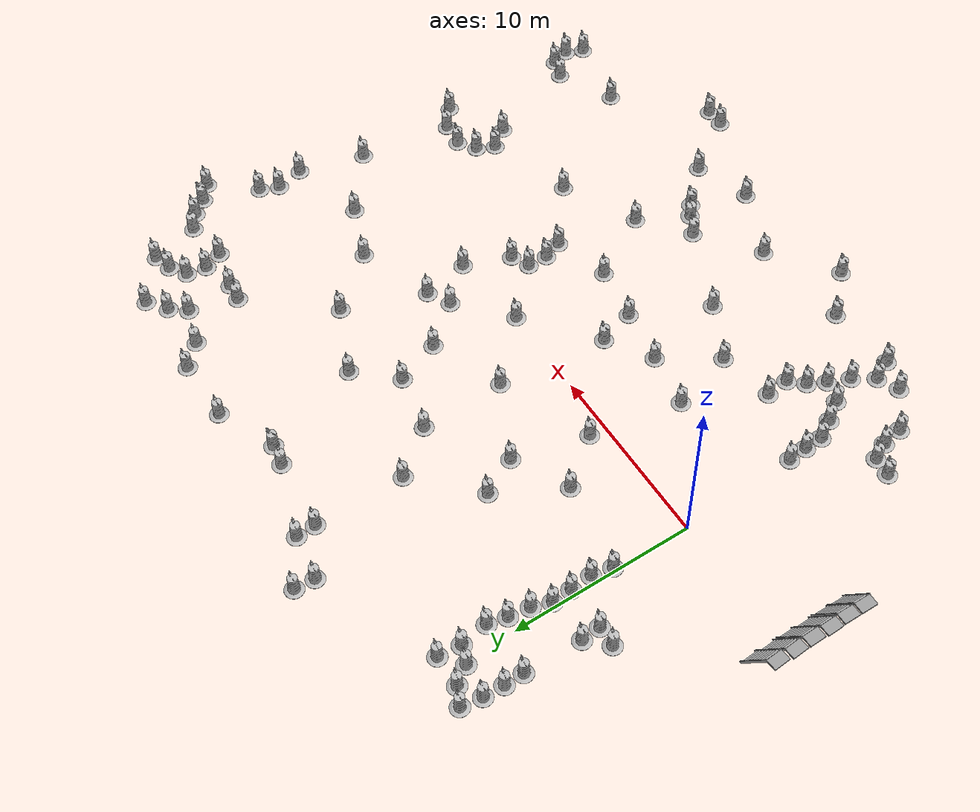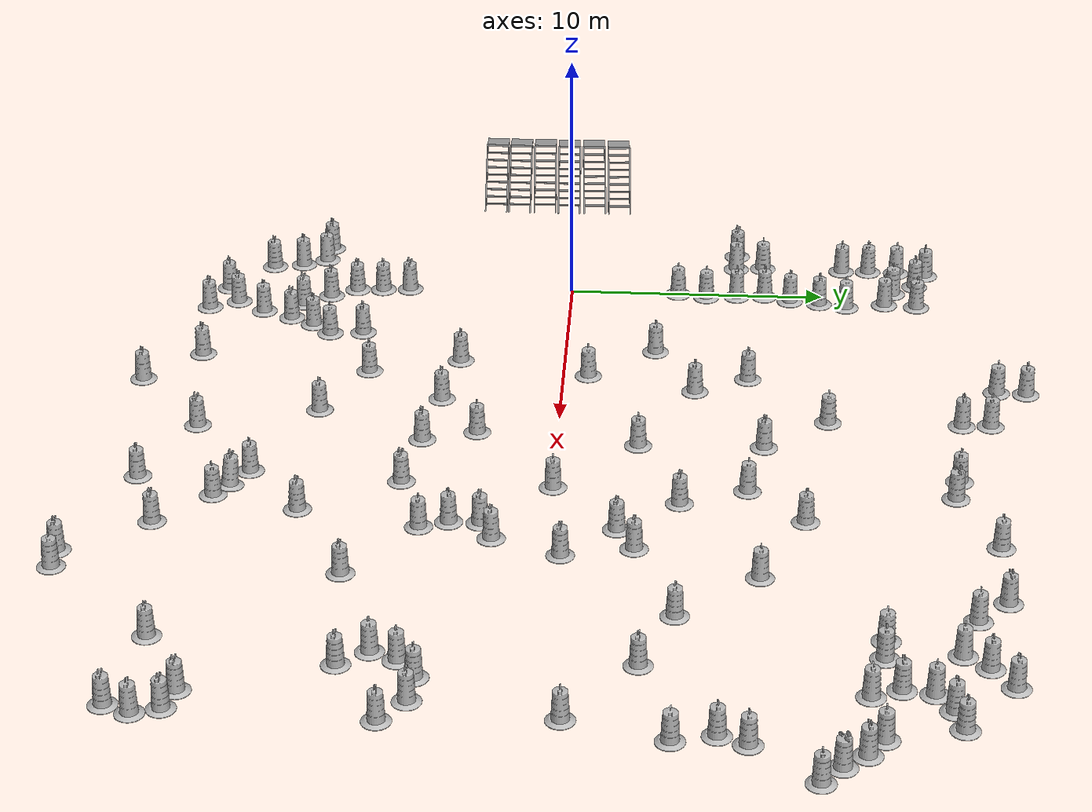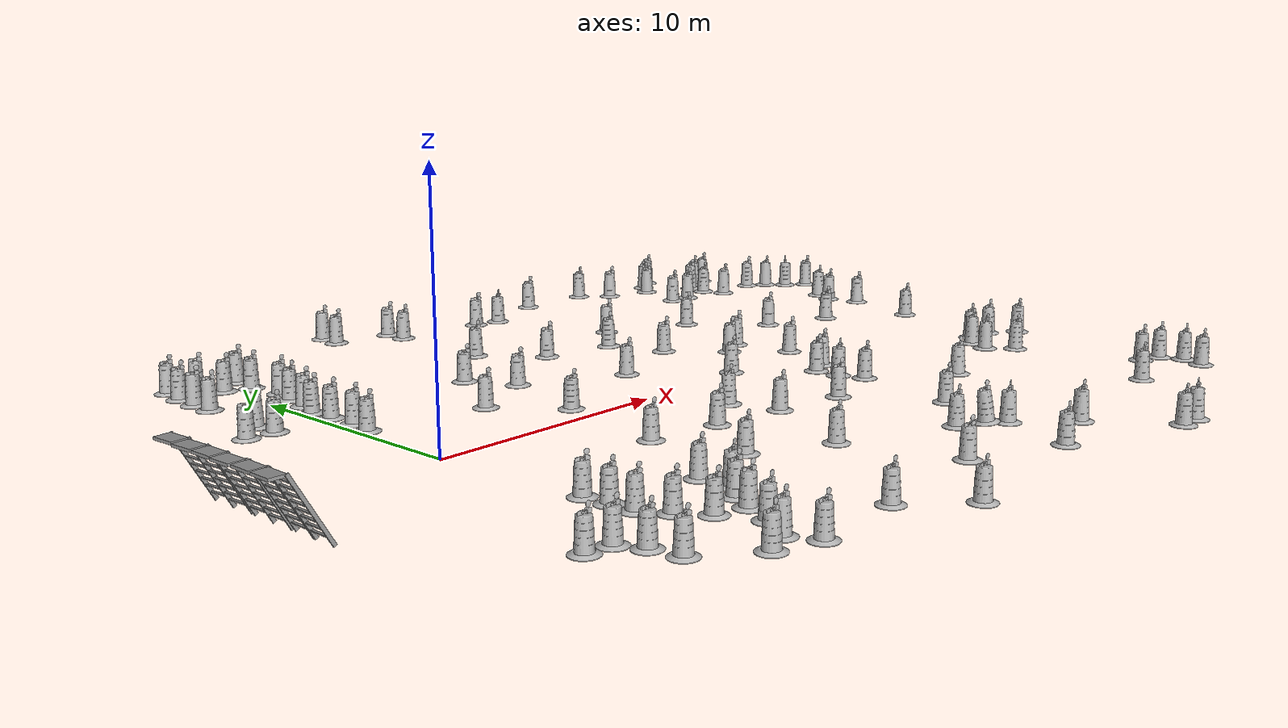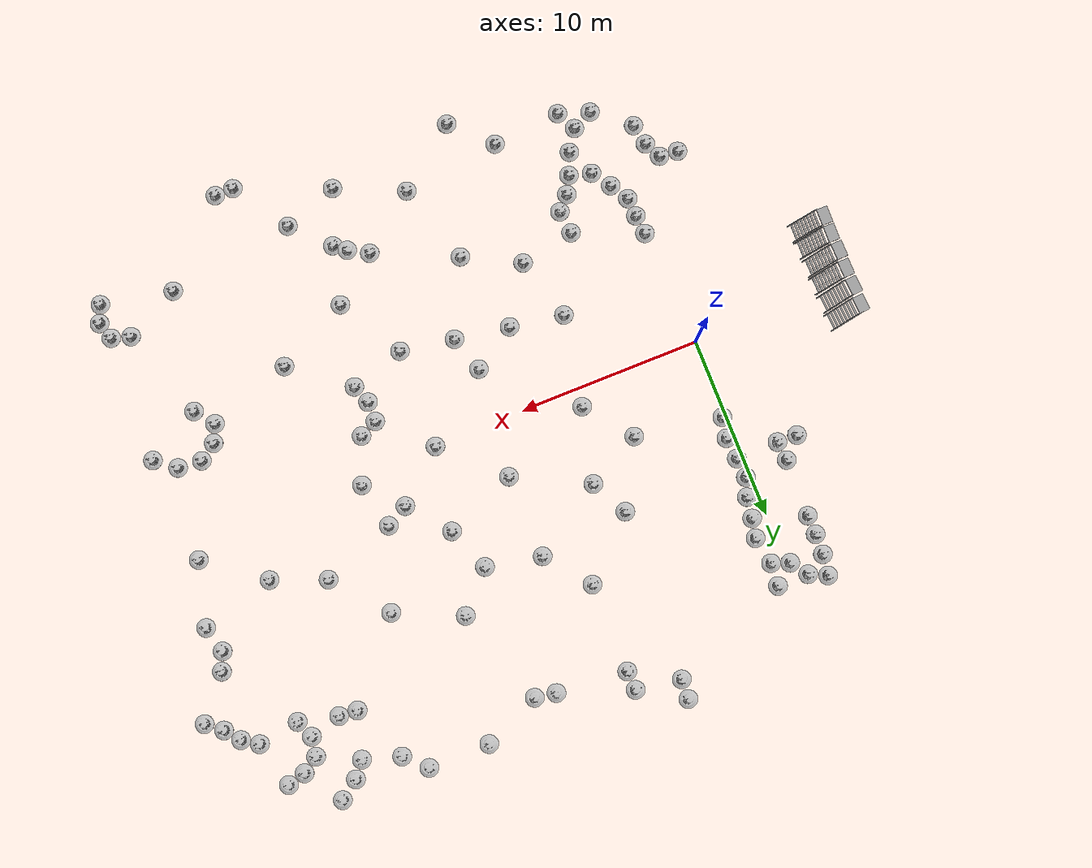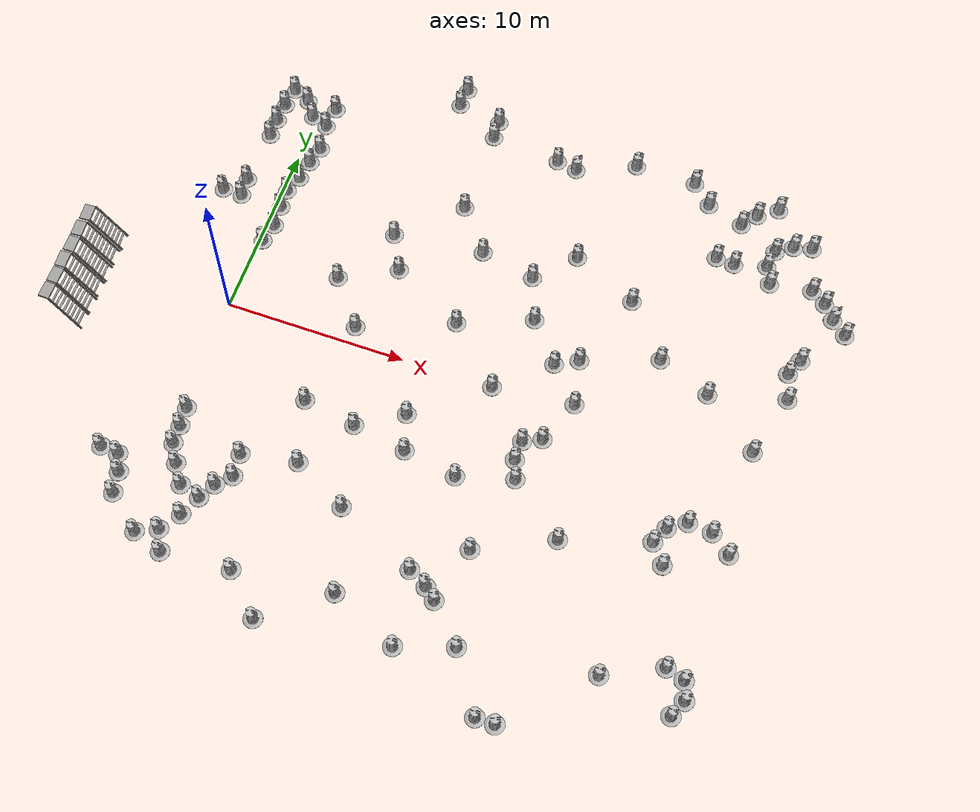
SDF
<sdf version="1.4">
 <world name="IGVC_Advanced_Course">
  <light name="sun" type="directional">
   <pose>0 0 10 0 -0 0</pose>
   <diffuse>0.8 0.8 0.8 1</diffuse>
   <specular>0.2 0.2 0.2 1</specular>
   <attenuation>
    <range>1000</range>
    <constant>0.9</constant>
    <linear>0.01</linear>
    <quadratic>0.001</quadratic>
   </attenuation>
   <direction>-0.5 0.1 -0.9</direction>
  </light>
  <physics type="ode">
   <max_step_size>0.001</max_step_size>
   <real_time_factor>1</real_time_factor>
   <real_time_update_rate>1000</real_time_update_rate>
   <gravity>0 0 -9.8</gravity>
  </physics>
  <scene><ambient>0.4 0.4 0.4 1</ambient><background>0.7 0.7 0.7 1</background><shadows>1</shadows></scene>
  <model name="Construction Barrel">
   <link name="link">
    <inertial>
     <pose>0 0 0.4 0 -0 0</pose>
     <mass>500</mass>
     <inertia><ixx>51.2096</ixx><iyy>51.2096</iyy><izz>25</izz><ixy>0</ixy><ixz>0</ixz><iyz>0</iyz></inertia>
    </inertial>
    <collision name="collision">
     <geometry><mesh><uri>model://construction_barrel/meshes/construction_barrel.dae</uri></mesh></geometry>
    </collision>
    <visual name="visual">
     <geometry><mesh><uri>model://construction_barrel/meshes/construction_barrel.dae</uri></mesh></geometry>
    </visual>
    <velocity_decay><linear>0</linear><angular>0</angular></velocity_decay>
   </link>
   <pose>2.90937 -10.9413 0.081 2e-06 1.05879e-22 -0.206638</pose>
   <static>0</static>
  </model>
  <model name="Construction Barrel_0">
   <link name="link">
    <inertial>
     <pose>0 0 0.4 0 -0 0</pose>
     <mass>500</mass>
     <inertia><ixx>51.2096</ixx><iyy>51.2096</iyy><izz>25</izz><ixy>0</ixy><ixz>0</ixz><iyz>0</iyz></inertia>
    </inertial>
    <collision name="collision">
     <geometry><mesh><uri>model://construction_barrel/meshes/construction_barrel.dae</uri></mesh></geometry>
    </collision>
    <visual name="visual">
     <geometry><mesh><uri>model://construction_barrel/meshes/construction_barrel.dae</uri></mesh></geometry>
    </visual>
    <velocity_decay><linear>0</linear><angular>0</angular></velocity_decay>
   </link>
   <pose>3.4058 -10.0126 0.080999 -2e-06 -3e-06 -0.053736</pose>
   <static>0</static>
  </model>
  <model name="Construction Barrel_1">
   <link name="link">
    <inertial>
     <pose>0 0 0.4 0 -0 0</pose>
     <mass>500</mass>
     <inertia><ixx>51.2096</ixx><iyy>51.2096</iyy><izz>25</izz><ixy>0</ixy><ixz>0</ixz><iyz>0</iyz></inertia>
    </inertial>
    <collision name="collision">
     <geometry><mesh><uri>model://construction_barrel/meshes/construction_barrel.dae</uri></mesh></geometry>
    </collision>
    <visual name="visual">
     <geometry><mesh><uri>model://construction_barrel/meshes/construction_barrel.dae</uri></mesh></geometry>
    </visual>
    <velocity_decay><linear>0</linear><angular>0</angular></velocity_decay>
   </link>
   <pose>4.10507 -9.27505 0.080999 -1e-06 -2e-06 0.216739</pose>
   <static>0</static>
  </model>
  <model name="Construction Barrel_2">
   <link name="link">
    <inertial>
     <pose>0 0 0.4 0 -0 0</pose>
     <mass>500</mass>
     <inertia><ixx>51.2096</ixx><iyy>51.2096</iyy><izz>25</izz><ixy>0</ixy><ixz>0</ixz><iyz>0</iyz></inertia>
    </inertial>
    <collision name="collision">
     <geometry><mesh><uri>model://construction_barrel/meshes/construction_barrel.dae</uri></mesh></geometry>
    </collision>
    <visual name="visual">
     <geometry><mesh><uri>model://construction_barrel/meshes/construction_barrel.dae</uri></mesh></geometry>
    </visual>
    <velocity_decay><linear>0</linear><angular>0</angular></velocity_decay>
   </link>
   <pose>3.97762 -7.99254 0.080999 -1e-06 -3e-06 -0.029562</pose>
   <static>0</static>
  </model>
  <model name="Construction Barrel_3">
   <link name="link">
    <inertial>
     <pose>0 0 0.4 0 -0 0</pose>
     <mass>500</mass>
     <inertia><ixx>51.2096</ixx><iyy>51.2096</iyy><izz>25</izz><ixy>0</ixy><ixz>0</ixz><iyz>0</iyz></inertia>
    </inertial>
    <collision name="collision">
     <geometry><mesh><uri>model://construction_barrel/meshes/construction_barrel.dae</uri></mesh></geometry>
    </collision>
    <visual name="visual">
     <geometry><mesh><uri>model://construction_barrel/meshes/construction_barrel.dae</uri></mesh></geometry>
    </visual>
    <velocity_decay><linear>0</linear><angular>0</angular></velocity_decay>
   </link>
   <pose>0.55482 -13.7328 0.080999 -1e-06 -3e-06 -0.003573</pose>
   <static>0</static>
  </model>
  <model name="Construction Barrel_4">
   <link name="link">
    <inertial>
     <pose>0 0 0.4 0 -0 0</pose>
     <mass>500</mass>
     <inertia><ixx>51.2096</ixx><iyy>51.2096</iyy><izz>25</izz><ixy>0</ixy><ixz>0</ixz><iyz>0</iyz></inertia>
    </inertial>
    <collision name="collision">
     <geometry><mesh><uri>model://construction_barrel/meshes/construction_barrel.dae</uri></mesh></geometry>
    </collision>
    <visual name="visual">
     <geometry><mesh><uri>model://construction_barrel/meshes/construction_barrel.dae</uri></mesh></geometry>
    </visual>
    <velocity_decay><linear>0</linear><angular>0</angular></velocity_decay>
   </link>
   <pose>1.67439 -13.2098 0.080999 -2e-06 -4e-06 -0.033039</pose>
   <static>0</static>
  </model>
  <model name="Construction Barrel_5">
   <link name="link">
    <inertial>
     <pose>0 0 0.4 0 -0 0</pose>
     <mass>500</mass>
     <inertia><ixx>51.2096</ixx><iyy>51.2096</iyy><izz>25</izz><ixy>0</ixy><ixz>0</ixz><iyz>0</iyz></inertia>
    </inertial>
    <collision name="collision">
     <geometry><mesh><uri>model://construction_barrel/meshes/construction_barrel.dae</uri></mesh></geometry>
    </collision>
    <visual name="visual">
     <geometry><mesh><uri>model://construction_barrel/meshes/construction_barrel.dae</uri></mesh></geometry>
    </visual>
    <velocity_decay><linear>0</linear><angular>0</angular></velocity_decay>
   </link>
   <pose>2.21677 -14.2989 0.080999 -2e-06 -4e-06 -0.077354</pose>
   <static>0</static>
  </model>
  <model name="Construction Barrel_6">
   <link name="link">
    <inertial>
     <pose>0 0 0.4 0 -0 0</pose>
     <mass>500</mass>
     <inertia><ixx>51.2096</ixx><iyy>51.2096</iyy><izz>25</izz><ixy>0</ixy><ixz>0</ixz><iyz>0</iyz></inertia>
    </inertial>
    <collision name="collision">
     <geometry><mesh><uri>model://construction_barrel/meshes/construction_barrel.dae</uri></mesh></geometry>
    </collision>
    <visual name="visual">
     <geometry><mesh><uri>model://construction_barrel/meshes/construction_barrel.dae</uri></mesh></geometry>
    </visual>
    <velocity_decay><linear>0</linear><angular>0</angular></velocity_decay>
   </link>
   <pose>7.98804 -15.9905 0.080999 5e-06 6.61744e-24 -0.006168</pose>
   <static>0</static>
  </model>
  <model name="Construction Barrel_7">
   <link name="link">
    <inertial>
     <pose>0 0 0.4 0 -0 0</pose>
     <mass>500</mass>
     <inertia><ixx>51.2096</ixx><iyy>51.2096</iyy><izz>25</izz><ixy>0</ixy><ixz>0</ixz><iyz>0</iyz></inertia>
    </inertial>
    <collision name="collision">
     <geometry><mesh><uri>model://construction_barrel/meshes/construction_barrel.dae</uri></mesh></geometry>
    </collision>
    <visual name="visual">
     <geometry><mesh><uri>model://construction_barrel/meshes/construction_barrel.dae</uri></mesh></geometry>
    </visual>
    <velocity_decay><linear>0</linear><angular>0</angular></velocity_decay>
   </link>
   <pose>5.97341 -14.0029 0.080999 3e-06 1e-06 -0.061146</pose>
   <static>0</static>
  </model>
  <model name="Construction Barrel_8">
   <link name="link">
    <inertial>
     <pose>0 0 0.4 0 -0 0</pose>
     <mass>500</mass>
     <inertia><ixx>51.2096</ixx><iyy>51.2096</iyy><izz>25</izz><ixy>0</ixy><ixz>0</ixz><iyz>0</iyz></inertia>
    </inertial>
    <collision name="collision">
     <geometry><mesh><uri>model://construction_barrel/meshes/construction_barrel.dae</uri></mesh></geometry>
    </collision>
    <visual name="visual">
     <geometry><mesh><uri>model://construction_barrel/meshes/construction_barrel.dae</uri></mesh></geometry>
    </visual>
    <velocity_decay><linear>0</linear><angular>0</angular></velocity_decay>
   </link>
   <pose>11.3381 -13.3903 0.080999 0 -3e-06 -0.1961</pose>
   <static>0</static>
  </model>
  <model name="Construction Barrel_9">
   <link name="link">
    <inertial>
     <pose>0 0 0.4 0 -0 0</pose>
     <mass>500</mass>
     <inertia><ixx>51.2096</ixx><iyy>51.2096</iyy><izz>25</izz><ixy>0</ixy><ixz>0</ixz><iyz>0</iyz></inertia>
    </inertial>
    <collision name="collision">
     <geometry><mesh><uri>model://construction_barrel/meshes/construction_barrel.dae</uri></mesh></geometry>
    </collision>
    <visual name="visual">
     <geometry><mesh><uri>model://construction_barrel/meshes/construction_barrel.dae</uri></mesh></geometry>
    </visual>
    <velocity_decay><linear>0</linear><angular>0</angular></velocity_decay>
   </link>
   <pose>14.444 -10.989 0.080999 -1e-06 -3e-06 0.066073</pose>
   <static>0</static>
  </model>
  <model name="Construction Barrel_10">
   <link name="link">
    <inertial>
     <pose>0 0 0.4 0 -0 0</pose>
     <mass>500</mass>
     <inertia><ixx>51.2096</ixx><iyy>51.2096</iyy><izz>25</izz><ixy>0</ixy><ixz>0</ixz><iyz>0</iyz></inertia>
    </inertial>
    <collision name="collision">
     <geometry><mesh><uri>model://construction_barrel/meshes/construction_barrel.dae</uri></mesh></geometry>
    </collision>
    <visual name="visual">
     <geometry><mesh><uri>model://construction_barrel/meshes/construction_barrel.dae</uri></mesh></geometry>
    </visual>
    <velocity_decay><linear>0</linear><angular>0</angular></velocity_decay>
   </link>
   <pose>15.5108 -11.5852 0.132666 -0.044248 -0.091691 -0.232801</pose>
   <static>0</static>
  </model>
  <model name="Construction Barrel_11">
   <link name="link">
    <inertial>
     <pose>0 0 0.4 0 -0 0</pose>
     <mass>500</mass>
     <inertia><ixx>51.2096</ixx><iyy>51.2096</iyy><izz>25</izz><ixy>0</ixy><ixz>0</ixz><iyz>0</iyz></inertia>
    </inertial>
    <collision name="collision">
     <geometry><mesh><uri>model://construction_barrel/meshes/construction_barrel.dae</uri></mesh></geometry>
    </collision>
    <visual name="visual">
     <geometry><mesh><uri>model://construction_barrel/meshes/construction_barrel.dae</uri></mesh></geometry>
    </visual>
    <velocity_decay><linear>0</linear><angular>0</angular></velocity_decay>
   </link>
   <pose>16.1396 -12.1013 0.081 0 -0 0.23185</pose>
   <static>0</static>
  </model>
  <model name="Construction Barrel_12">
   <link name="link">
    <inertial>
     <pose>0 0 0.4 0 -0 0</pose>
     <mass>500</mass>
     <inertia><ixx>51.2096</ixx><iyy>51.2096</iyy><izz>25</izz><ixy>0</ixy><ixz>0</ixz><iyz>0</iyz></inertia>
    </inertial>
    <collision name="collision">
     <geometry><mesh><uri>model://construction_barrel/meshes/construction_barrel.dae</uri></mesh></geometry>
    </collision>
    <visual name="visual">
     <geometry><mesh><uri>model://construction_barrel/meshes/construction_barrel.dae</uri></mesh></geometry>
    </visual>
    <velocity_decay><linear>0</linear><angular>0</angular></velocity_decay>
   </link>
   <pose>25.0067 -13.0004 0.080999 3e-06 -0 0.001655</pose>
   <static>0</static>
  </model>
  <model name="Construction Barrel_13">
   <link name="link">
    <inertial>
     <pose>0 0 0.4 0 -0 0</pose>
     <mass>500</mass>
     <inertia><ixx>51.2096</ixx><iyy>51.2096</iyy><izz>25</izz><ixy>0</ixy><ixz>0</ixz><iyz>0</iyz></inertia>
    </inertial>
    <collision name="collision">
     <geometry><mesh><uri>model://construction_barrel/meshes/construction_barrel.dae</uri></mesh></geometry>
    </collision>
    <visual name="visual">
     <geometry><mesh><uri>model://construction_barrel/meshes/construction_barrel.dae</uri></mesh></geometry>
    </visual>
    <velocity_decay><linear>0</linear><angular>0</angular></velocity_decay>
   </link>
   <pose>28.909 -13.7683 0.080999 -1e-06 -3e-06 -0.096455</pose>
   <static>0</static>
  </model>
  <model name="Construction Barrel_14">
   <link name="link">
    <inertial>
     <pose>0 0 0.4 0 -0 0</pose>
     <mass>500</mass>
     <inertia><ixx>51.2096</ixx><iyy>51.2096</iyy><izz>25</izz><ixy>0</ixy><ixz>0</ixz><iyz>0</iyz></inertia>
    </inertial>
    <collision name="collision">
     <geometry><mesh><uri>model://construction_barrel/meshes/construction_barrel.dae</uri></mesh></geometry>
    </collision>
    <visual name="visual">
     <geometry><mesh><uri>model://construction_barrel/meshes/construction_barrel.dae</uri></mesh></geometry>
    </visual>
    <velocity_decay><linear>0</linear><angular>0</angular></velocity_decay>
   </link>
   <pose>29.3138 -12.8312 0.080999 -1e-06 -3e-06 0.021451</pose>
   <static>0</static>
  </model>
  <model name="Construction Barrel_15">
   <link name="link">
    <inertial>
     <pose>0 0 0.4 0 -0 0</pose>
     <mass>500</mass>
     <inertia><ixx>51.2096</ixx><iyy>51.2096</iyy><izz>25</izz><ixy>0</ixy><ixz>0</ixz><iyz>0</iyz></inertia>
    </inertial>
    <collision name="collision">
     <geometry><mesh><uri>model://construction_barrel/meshes/construction_barrel.dae</uri></mesh></geometry>
    </collision>
    <visual name="visual">
     <geometry><mesh><uri>model://construction_barrel/meshes/construction_barrel.dae</uri></mesh></geometry>
    </visual>
    <velocity_decay><linear>0</linear><angular>0</angular></velocity_decay>
   </link>
   <pose>29.0176 -11.8596 0.080999 -1e-06 -2e-06 -0.086565</pose>
   <static>0</static>
  </model>
  <model name="Construction Barrel_16">
   <link name="link">
    <inertial>
     <pose>0 0 0.4 0 -0 0</pose>
     <mass>500</mass>
     <inertia><ixx>51.2096</ixx><iyy>51.2096</iyy><izz>25</izz><ixy>0</ixy><ixz>0</ixz><iyz>0</iyz></inertia>
    </inertial>
    <collision name="collision">
     <geometry><mesh><uri>model://construction_barrel/meshes/construction_barrel.dae</uri></mesh></geometry>
    </collision>
    <visual name="visual">
     <geometry><mesh><uri>model://construction_barrel/meshes/construction_barrel.dae</uri></mesh></geometry>
    </visual>
    <velocity_decay><linear>0</linear><angular>0</angular></velocity_decay>
   </link>
   <pose>28.002 -11.5393 0.080999 -1e-06 -3e-06 -0.166182</pose>
   <static>0</static>
  </model>
  <model name="Construction Barrel_17">
   <link name="link">
    <inertial>
     <pose>0 0 0.4 0 -0 0</pose>
     <mass>500</mass>
     <inertia><ixx>51.2096</ixx><iyy>51.2096</iyy><izz>25</izz><ixy>0</ixy><ixz>0</ixz><iyz>0</iyz></inertia>
    </inertial>
    <collision name="collision">
     <geometry><mesh><uri>model://construction_barrel/meshes/construction_barrel.dae</uri></mesh></geometry>
    </collision>
    <visual name="visual">
     <geometry><mesh><uri>model://construction_barrel/meshes/construction_barrel.dae</uri></mesh></geometry>
    </visual>
    <velocity_decay><linear>0</linear><angular>0</angular></velocity_decay>
   </link>
   <pose>26.3344 -6.52818 0.080999 -1e-06 -2e-06 -0.088087</pose>
   <static>0</static>
  </model>
  <model name="Construction Barrel_18">
   <link name="link">
    <inertial>
     <pose>0 0 0.4 0 -0 0</pose>
     <mass>500</mass>
     <inertia><ixx>51.2096</ixx><iyy>51.2096</iyy><izz>25</izz><ixy>0</ixy><ixz>0</ixz><iyz>0</iyz></inertia>
    </inertial>
    <collision name="collision">
     <geometry><mesh><uri>model://construction_barrel/meshes/construction_barrel.dae</uri></mesh></geometry>
    </collision>
    <visual name="visual">
     <geometry><mesh><uri>model://construction_barrel/meshes/construction_barrel.dae</uri></mesh></geometry>
    </visual>
    <velocity_decay><linear>0</linear><angular>0</angular></velocity_decay>
   </link>
   <pose>20.9537 -6.98032 0.080999 -1e-06 -3e-06 -0.078884</pose>
   <static>0</static>
  </model>
  <model name="Construction Barrel_19">
   <link name="link">
    <inertial>
     <pose>0 0 0.4 0 -0 0</pose>
     <mass>500</mass>
     <inertia><ixx>51.2096</ixx><iyy>51.2096</iyy><izz>25</izz><ixy>0</ixy><ixz>0</ixz><iyz>0</iyz></inertia>
    </inertial>
    <collision name="collision">
     <geometry><mesh><uri>model://construction_barrel/meshes/construction_barrel.dae</uri></mesh></geometry>
    </collision>
    <visual name="visual">
     <geometry><mesh><uri>model://construction_barrel/meshes/construction_barrel.dae</uri></mesh></geometry>
    </visual>
    <velocity_decay><linear>0</linear><angular>0</angular></velocity_decay>
   </link>
   <pose>16.9409 -8.96894 0.080999 -1e-06 -4e-06 -0.129432</pose>
   <static>0</static>
  </model>
  <model name="Construction Barrel_20">
   <link name="link">
    <inertial>
     <pose>0 0 0.4 0 -0 0</pose>
     <mass>500</mass>
     <inertia><ixx>51.2096</ixx><iyy>51.2096</iyy><izz>25</izz><ixy>0</ixy><ixz>0</ixz><iyz>0</iyz></inertia>
    </inertial>
    <collision name="collision">
     <geometry><mesh><uri>model://construction_barrel/meshes/construction_barrel.dae</uri></mesh></geometry>
    </collision>
    <visual name="visual">
     <geometry><mesh><uri>model://construction_barrel/meshes/construction_barrel.dae</uri></mesh></geometry>
    </visual>
    <velocity_decay><linear>0</linear><angular>0</angular></velocity_decay>
   </link>
   <pose>14.8941 -5.45377 0.080999 -1e-06 -2e-06 -0.261305</pose>
   <static>0</static>
  </model>
  <model name="Construction Barrel_21">
   <link name="link">
    <inertial>
     <pose>0 0 0.4 0 -0 0</pose>
     <mass>500</mass>
     <inertia><ixx>51.2096</ixx><iyy>51.2096</iyy><izz>25</izz><ixy>0</ixy><ixz>0</ixz><iyz>0</iyz></inertia>
    </inertial>
    <collision name="collision">
     <geometry><mesh><uri>model://construction_barrel/meshes/construction_barrel.dae</uri></mesh></geometry>
    </collision>
    <visual name="visual">
     <geometry><mesh><uri>model://construction_barrel/meshes/construction_barrel.dae</uri></mesh></geometry>
    </visual>
    <velocity_decay><linear>0</linear><angular>0</angular></velocity_decay>
   </link>
   <pose>17.5037 -3.53423 0.080999 -2e-06 -3e-06 0.256139</pose>
   <static>0</static>
  </model>
  <model name="Construction Barrel_22">
   <link name="link">
    <inertial>
     <pose>0 0 0.4 0 -0 0</pose>
     <mass>500</mass>
     <inertia><ixx>51.2096</ixx><iyy>51.2096</iyy><izz>25</izz><ixy>0</ixy><ixz>0</ixz><iyz>0</iyz></inertia>
    </inertial>
    <collision name="collision">
     <geometry><mesh><uri>model://construction_barrel/meshes/construction_barrel.dae</uri></mesh></geometry>
    </collision>
    <visual name="visual">
     <geometry><mesh><uri>model://construction_barrel/meshes/construction_barrel.dae</uri></mesh></geometry>
    </visual>
    <velocity_decay><linear>0</linear><angular>0</angular></velocity_decay>
   </link>
   <pose>25.9833 -4.54218 0.080999 3e-06 -1.32349e-23 0.019575</pose>
   <static>0</static>
  </model>
  <model name="Construction Barrel_23">
   <link name="link">
    <inertial>
     <pose>0 0 0.4 0 -0 0</pose>
     <mass>500</mass>
     <inertia><ixx>51.2096</ixx><iyy>51.2096</iyy><izz>25</izz><ixy>0</ixy><ixz>0</ixz><iyz>0</iyz></inertia>
    </inertial>
    <collision name="collision">
     <geometry><mesh><uri>model://construction_barrel/meshes/construction_barrel.dae</uri></mesh></geometry>
    </collision>
    <visual name="visual">
     <geometry><mesh><uri>model://construction_barrel/meshes/construction_barrel.dae</uri></mesh></geometry>
    </visual>
    <velocity_decay><linear>0</linear><angular>0</angular></velocity_decay>
   </link>
   <pose>25.5392 -5.49243 0.080999 -1e-06 -2e-06 0.03129</pose>
   <static>0</static>
  </model>
  <model name="Construction Barrel_24">
   <link name="link">
    <inertial>
     <pose>0 0 0.4 0 -0 0</pose>
     <mass>500</mass>
     <inertia><ixx>51.2096</ixx><iyy>51.2096</iyy><izz>25</izz><ixy>0</ixy><ixz>0</ixz><iyz>0</iyz></inertia>
    </inertial>
    <collision name="collision">
     <geometry><mesh><uri>model://construction_barrel/meshes/construction_barrel.dae</uri></mesh></geometry>
    </collision>
    <visual name="visual">
     <geometry><mesh><uri>model://construction_barrel/meshes/construction_barrel.dae</uri></mesh></geometry>
    </visual>
    <velocity_decay><linear>0</linear><angular>0</angular></velocity_decay>
   </link>
   <pose>26.9167 -3.89784 0.080999 4e-06 -0 7.9e-05</pose>
   <static>0</static>
  </model>
  <model name="Construction Barrel_25">
   <link name="link">
    <inertial>
     <pose>0 0 0.4 0 -0 0</pose>
     <mass>500</mass>
     <inertia><ixx>51.2096</ixx><iyy>51.2096</iyy><izz>25</izz><ixy>0</ixy><ixz>0</ixz><iyz>0</iyz></inertia>
    </inertial>
    <collision name="collision">
     <geometry><mesh><uri>model://construction_barrel/meshes/construction_barrel.dae</uri></mesh></geometry>
    </collision>
    <visual name="visual">
     <geometry><mesh><uri>model://construction_barrel/meshes/construction_barrel.dae</uri></mesh></geometry>
    </visual>
    <velocity_decay><linear>0</linear><angular>0</angular></velocity_decay>
   </link>
   <pose>28.2333 -4.01245 0.080999 2e-06 -2.64698e-23 -0.085916</pose>
   <static>0</static>
  </model>
  <model name="Construction Barrel_26">
   <link name="link">
    <inertial>
     <pose>0 0 0.4 0 -0 0</pose>
     <mass>500</mass>
     <inertia><ixx>51.2096</ixx><iyy>51.2096</iyy><izz>25</izz><ixy>0</ixy><ixz>0</ixz><iyz>0</iyz></inertia>
    </inertial>
    <collision name="collision">
     <geometry><mesh><uri>model://construction_barrel/meshes/construction_barrel.dae</uri></mesh></geometry>
    </collision>
    <visual name="visual">
     <geometry><mesh><uri>model://construction_barrel/meshes/construction_barrel.dae</uri></mesh></geometry>
    </visual>
    <velocity_decay><linear>0</linear><angular>0</angular></velocity_decay>
   </link>
   <pose>29.3369 -4.88549 0.080999 2e-06 1.32349e-23 -0.048616</pose>
   <static>0</static>
  </model>
  <model name="Construction Barrel_27">
   <link name="link">
    <inertial>
     <pose>0 0 0.4 0 -0 0</pose>
     <mass>500</mass>
     <inertia><ixx>51.2096</ixx><iyy>51.2096</iyy><izz>25</izz><ixy>0</ixy><ixz>0</ixz><iyz>0</iyz></inertia>
    </inertial>
    <collision name="collision">
     <geometry><mesh><uri>model://construction_barrel/meshes/construction_barrel.dae</uri></mesh></geometry>
    </collision>
    <visual name="visual">
     <geometry><mesh><uri>model://construction_barrel/meshes/construction_barrel.dae</uri></mesh></geometry>
    </visual>
    <velocity_decay><linear>0</linear><angular>0</angular></velocity_decay>
   </link>
   <pose>17.5233 -2.41916 0.081 2e-06 5.29396e-23 -0.167893</pose>
   <static>0</static>
  </model>
  <model name="Construction Barrel_28">
   <link name="link">
    <inertial>
     <pose>0 0 0.4 0 -0 0</pose>
     <mass>500</mass>
     <inertia><ixx>51.2096</ixx><iyy>51.2096</iyy><izz>25</izz><ixy>0</ixy><ixz>0</ixz><iyz>0</iyz></inertia>
    </inertial>
    <collision name="collision">
     <geometry><mesh><uri>model://construction_barrel/meshes/construction_barrel.dae</uri></mesh></geometry>
    </collision>
    <visual name="visual">
     <geometry><mesh><uri>model://construction_barrel/meshes/construction_barrel.dae</uri></mesh></geometry>
    </visual>
    <velocity_decay><linear>0</linear><angular>0</angular></velocity_decay>
   </link>
   <pose>18.497 -1.96191 0.080999 -1e-06 -3e-06 -0.115255</pose>
   <static>0</static>
  </model>
  <model name="Construction Barrel_29">
   <link name="link">
    <inertial>
     <pose>0 0 0.4 0 -0 0</pose>
     <mass>500</mass>
     <inertia><ixx>51.2096</ixx><iyy>51.2096</iyy><izz>25</izz><ixy>0</ixy><ixz>0</ixz><iyz>0</iyz></inertia>
    </inertial>
    <collision name="collision">
     <geometry><mesh><uri>model://construction_barrel/meshes/construction_barrel.dae</uri></mesh></geometry>
    </collision>
    <visual name="visual">
     <geometry><mesh><uri>model://construction_barrel/meshes/construction_barrel.dae</uri></mesh></geometry>
    </visual>
    <velocity_decay><linear>0</linear><angular>0</angular></velocity_decay>
   </link>
   <pose>17.8771 -4.56521 0.080999 3e-06 -0 0.056296</pose>
   <static>0</static>
  </model>
  <model name="Construction Barrel_30">
   <link name="link">
    <inertial>
     <pose>0 0 0.4 0 -0 0</pose>
     <mass>500</mass>
     <inertia><ixx>51.2096</ixx><iyy>51.2096</iyy><izz>25</izz><ixy>0</ixy><ixz>0</ixz><iyz>0</iyz></inertia>
    </inertial>
    <collision name="collision">
     <geometry><mesh><uri>model://construction_barrel/meshes/construction_barrel.dae</uri></mesh></geometry>
    </collision>
    <visual name="visual">
     <geometry><mesh><uri>model://construction_barrel/meshes/construction_barrel.dae</uri></mesh></geometry>
    </visual>
    <velocity_decay><linear>0</linear><angular>0</angular></velocity_decay>
   </link>
   <pose>6.00139 -3.99795 0.081 -1e-06 -2e-06 -0.034864</pose>
   <static>0</static>
  </model>
  <model name="Construction Barrel_31">
   <link name="link">
    <inertial>
     <pose>0 0 0.4 0 -0 0</pose>
     <mass>500</mass>
     <inertia><ixx>51.2096</ixx><iyy>51.2096</iyy><izz>25</izz><ixy>0</ixy><ixz>0</ixz><iyz>0</iyz></inertia>
    </inertial>
    <collision name="collision">
     <geometry><mesh><uri>model://construction_barrel/meshes/construction_barrel.dae</uri></mesh></geometry>
    </collision>
    <visual name="visual">
     <geometry><mesh><uri>model://construction_barrel/meshes/construction_barrel.dae</uri></mesh></geometry>
    </visual>
    <velocity_decay><linear>0</linear><angular>0</angular></velocity_decay>
   </link>
   <pose>6.98086 -7.43129 0.080999 -1e-06 -3e-06 -0.013448</pose>
   <static>0</static>
  </model>
  <model name="Construction Barrel_32">
   <link name="link">
    <inertial>
     <pose>0 0 0.4 0 -0 0</pose>
     <mass>500</mass>
     <inertia><ixx>51.2096</ixx><iyy>51.2096</iyy><izz>25</izz><ixy>0</ixy><ixz>0</ixz><iyz>0</iyz></inertia>
    </inertial>
    <collision name="collision">
     <geometry><mesh><uri>model://construction_barrel/meshes/construction_barrel.dae</uri></mesh></geometry>
    </collision>
    <visual name="visual">
     <geometry><mesh><uri>model://construction_barrel/meshes/construction_barrel.dae</uri></mesh></geometry>
    </visual>
    <velocity_decay><linear>0</linear><angular>0</angular></velocity_decay>
   </link>
   <pose>8.94769 -4.48615 0.080999 -1e-06 -3e-06 -0.121942</pose>
   <static>0</static>
  </model>
  <model name="Construction Barrel_33">
   <link name="link">
    <inertial>
     <pose>0 0 0.4 0 -0 0</pose>
     <mass>500</mass>
     <inertia><ixx>51.2096</ixx><iyy>51.2096</iyy><izz>25</izz><ixy>0</ixy><ixz>0</ixz><iyz>0</iyz></inertia>
    </inertial>
    <collision name="collision">
     <geometry><mesh><uri>model://construction_barrel/meshes/construction_barrel.dae</uri></mesh></geometry>
    </collision>
    <visual name="visual">
     <geometry><mesh><uri>model://construction_barrel/meshes/construction_barrel.dae</uri></mesh></geometry>
    </visual>
    <velocity_decay><linear>0</linear><angular>0</angular></velocity_decay>
   </link>
   <pose>9.99154 -8.99122 0.080999 -1e-06 -5e-06 -0.041963</pose>
   <static>0</static>
  </model>
  <model name="Construction Barrel_34">
   <link name="link">
    <inertial>
     <pose>0 0 0.4 0 -0 0</pose>
     <mass>500</mass>
     <inertia><ixx>51.2096</ixx><iyy>51.2096</iyy><izz>25</izz><ixy>0</ixy><ixz>0</ixz><iyz>0</iyz></inertia>
    </inertial>
    <collision name="collision">
     <geometry><mesh><uri>model://construction_barrel/meshes/construction_barrel.dae</uri></mesh></geometry>
    </collision>
    <visual name="visual">
     <geometry><mesh><uri>model://construction_barrel/meshes/construction_barrel.dae</uri></mesh></geometry>
    </visual>
    <velocity_decay><linear>0</linear><angular>0</angular></velocity_decay>
   </link>
   <pose>11.3293 -2.97512 0.080999 4e-06 -2.64698e-23 0.058727</pose>
   <static>0</static>
  </model>
  <model name="ladder_60deg_0rails">
   <static>1</static>
   <link name="step0">
    <pose>0 0.15396 0.266667 0 -0 0</pose>
    <inertial>
     <mass>9.75482</mass>
     <inertia>
      <ixx>0.00957124</ixx>
      <iyy>0.65963</iyy>
      <izz>0.666842</izz>
      <ixy>0</ixy>
      <ixz>0</ixz>
      <iyz>0</iyz>
     </inertia>
    </inertial>
    <collision name="collision"><geometry><box><size>0.9 0.1016 0.0381</size></box></geometry></collision>
    <visual name="visual">
     <geometry><box><size>0.9 0.1016 0.0381</size></box></geometry>
     <material>
      <script><uri>file://media/materials/scripts/gazebo.material</uri><name>Gazebo/Grey</name></script>
     </material>
    </visual>
    <velocity_decay><linear>0</linear><angular>0</angular></velocity_decay>
   </link>
   <link name="step1">
    <pose>0 0.30792 0.533333 0 -0 0</pose>
    <inertial>
     <mass>9.75482</mass>
     <inertia>
      <ixx>0.00957124</ixx>
      <iyy>0.65963</iyy>
      <izz>0.666842</izz>
      <ixy>0</ixy>
      <ixz>0</ixz>
      <iyz>0</iyz>
     </inertia>
    </inertial>
    <collision name="collision"><geometry><box><size>0.9 0.1016 0.0381</size></box></geometry></collision>
    <visual name="visual">
     <geometry><box><size>0.9 0.1016 0.0381</size></box></geometry>
     <material>
      <script><uri>file://media/materials/scripts/gazebo.material</uri><name>Gazebo/Grey</name></script>
     </material>
    </visual>
    <velocity_decay><linear>0</linear><angular>0</angular></velocity_decay>
   </link>
   <link name="step2">
    <pose>0 0.46188 0.8 0 -0 0</pose>
    <inertial>
     <mass>9.75482</mass>
     <inertia>
      <ixx>0.00957124</ixx>
      <iyy>0.65963</iyy>
      <izz>0.666842</izz>
      <ixy>0</ixy>
      <ixz>0</ixz>
      <iyz>0</iyz>
     </inertia>
    </inertial>
    <collision name="collision"><geometry><box><size>0.9 0.1016 0.0381</size></box></geometry></collision>
    <visual name="visual">
     <geometry><box><size>0.9 0.1016 0.0381</size></box></geometry>
     <material>
      <script><uri>file://media/materials/scripts/gazebo.material</uri><name>Gazebo/Grey</name></script>
     </material>
    </visual>
    <velocity_decay><linear>0</linear><angular>0</angular></velocity_decay>
   </link>
   <link name="step3">
    <pose>0 0.61584 1.06667 0 -0 0</pose>
    <inertial>
     <mass>9.75482</mass>
     <inertia>
      <ixx>0.00957124</ixx>
      <iyy>0.65963</iyy>
      <izz>0.666842</izz>
      <ixy>0</ixy>
      <ixz>0</ixz>
      <iyz>0</iyz>
     </inertia>
    </inertial>
    <collision name="collision"><geometry><box><size>0.9 0.1016 0.0381</size></box></geometry></collision>
    <visual name="visual">
     <geometry><box><size>0.9 0.1016 0.0381</size></box></geometry>
     <material>
      <script><uri>file://media/materials/scripts/gazebo.material</uri><name>Gazebo/Grey</name></script>
     </material>
    </visual>
    <velocity_decay><linear>0</linear><angular>0</angular></velocity_decay>
   </link>
   <link name="step4">
    <pose>0 0.7698 1.33333 0 -0 0</pose>
    <inertial>
     <mass>9.75482</mass>
     <inertia>
      <ixx>0.00957124</ixx>
      <iyy>0.65963</iyy>
      <izz>0.666842</izz>
      <ixy>0</ixy>
      <ixz>0</ixz>
      <iyz>0</iyz>
     </inertia>
    </inertial>
    <collision name="collision"><geometry><box><size>0.9 0.1016 0.0381</size></box></geometry></collision>
    <visual name="visual">
     <geometry><box><size>0.9 0.1016 0.0381</size></box></geometry>
     <material>
      <script><uri>file://media/materials/scripts/gazebo.material</uri><name>Gazebo/Grey</name></script>
     </material>
    </visual>
    <velocity_decay><linear>0</linear><angular>0</angular></velocity_decay>
   </link>
   <link name="step5">
    <pose>0 0.92376 1.6 0 -0 0</pose>
    <inertial>
     <mass>9.75482</mass>
     <inertia>
      <ixx>0.00957124</ixx>
      <iyy>0.65963</iyy>
      <izz>0.666842</izz>
      <ixy>0</ixy>
      <ixz>0</ixz>
      <iyz>0</iyz>
     </inertia>
    </inertial>
    <collision name="collision"><geometry><box><size>0.9 0.1016 0.0381</size></box></geometry></collision>
    <visual name="visual">
     <geometry><box><size>0.9 0.1016 0.0381</size></box></geometry>
     <material>
      <script><uri>file://media/materials/scripts/gazebo.material</uri><name>Gazebo/Grey</name></script>
     </material>
    </visual>
    <velocity_decay><linear>0</linear><angular>0</angular></velocity_decay>
   </link>
   <link name="step6">
    <pose>0 1.07772 1.86667 0 -0 0</pose>
    <inertial>
     <mass>9.75482</mass>
     <inertia>
      <ixx>0.00957124</ixx>
      <iyy>0.65963</iyy>
      <izz>0.666842</izz>
      <ixy>0</ixy>
      <ixz>0</ixz>
      <iyz>0</iyz>
     </inertia>
    </inertial>
    <collision name="collision"><geometry><box><size>0.9 0.1016 0.0381</size></box></geometry></collision>
    <visual name="visual">
     <geometry><box><size>0.9 0.1016 0.0381</size></box></geometry>
     <material>
      <script><uri>file://media/materials/scripts/gazebo.material</uri><name>Gazebo/Grey</name></script>
     </material>
    </visual>
    <velocity_decay><linear>0</linear><angular>0</angular></velocity_decay>
   </link>
   <link name="step7">
    <pose>0 1.23168 2.13333 0 -0 0</pose>
    <inertial>
     <mass>9.75482</mass>
     <inertia>
      <ixx>0.00957124</ixx>
      <iyy>0.65963</iyy>
      <izz>0.666842</izz>
      <ixy>0</ixy>
      <ixz>0</ixz>
      <iyz>0</iyz>
     </inertia>
    </inertial>
    <collision name="collision"><geometry><box><size>0.9 0.1016 0.0381</size></box></geometry></collision>
    <visual name="visual">
     <geometry><box><size>0.9 0.1016 0.0381</size></box></geometry>
     <material>
      <script><uri>file://media/materials/scripts/gazebo.material</uri><name>Gazebo/Grey</name></script>
     </material>
    </visual>
    <velocity_decay><linear>0</linear><angular>0</angular></velocity_decay>
   </link>
   <link name="landing">
    <pose>0 1.68564 2.4 0 -0 0</pose>
    <inertial>
     <mass>57.6072</mass>
     <inertia><ixx>1.73518</ixx><iyy>3.89545</iyy><izz>5.6167</izz><ixy>0</ixy><ixz>0</ixz><iyz>0</iyz></inertia>
    </inertial>
    <collision name="collision"><geometry><box><size>0.9 0.6 0.1016</size></box></geometry></collision>
    <visual name="visual">
     <geometry><box><size>0.9 0.6 0.1016</size></box></geometry>
     <material>
      <script><uri>file://media/materials/scripts/gazebo.material</uri><name>Gazebo/Grey</name></script>
     </material>
    </visual>
    <velocity_decay><linear>0</linear><angular>0</angular></velocity_decay>
   </link>
   <link name="left_side_wall">
    <pose>-0.45 0.69282 1.2 1.0472 -0 0</pose>
    <collision name="collision"><geometry><box><size>0.0508 2.85128 0.13</size></box></geometry></collision>
    <visual name="visual">
     <geometry><box><size>0.0508 2.85128 0.13</size></box></geometry>
     <material>
      <script><uri>file://media/materials/scripts/gazebo.material</uri><name>Gazebo/Grey</name></script>
     </material>
    </visual>
    <velocity_decay><linear>0</linear><angular>0</angular></velocity_decay>
   </link>
   <link name="right_side_wall">
    <pose>0.45 0.69282 1.2 1.0472 -0 0</pose>
    <collision name="collision"><geometry><box><size>0.0508 2.85128 0.13</size></box></geometry></collision>
    <visual name="visual">
     <geometry><box><size>0.0508 2.85128 0.13</size></box></geometry>
     <material>
      <script><uri>file://media/materials/scripts/gazebo.material</uri><name>Gazebo/Grey</name></script>
     </material>
    </visual>
    <velocity_decay><linear>0</linear><angular>0</angular></velocity_decay>
   </link>
   <pose>-6.99475 -2.53648 0 0 -0 1.56</pose>
  </model>
  <model name="ladder_60deg_0rails_0">
   <static>1</static>
   <link name="step0">
    <pose>0 0.15396 0.266667 0 -0 0</pose>
    <inertial>
     <mass>9.75482</mass>
     <inertia>
      <ixx>0.00957124</ixx>
      <iyy>0.65963</iyy>
      <izz>0.666842</izz>
      <ixy>0</ixy>
      <ixz>0</ixz>
      <iyz>0</iyz>
     </inertia>
    </inertial>
    <collision name="collision"><geometry><box><size>0.9 0.1016 0.0381</size></box></geometry></collision>
    <visual name="visual">
     <geometry><box><size>0.9 0.1016 0.0381</size></box></geometry>
     <material>
      <script><uri>file://media/materials/scripts/gazebo.material</uri><name>Gazebo/Grey</name></script>
     </material>
    </visual>
    <velocity_decay><linear>0</linear><angular>0</angular></velocity_decay>
   </link>
   <link name="step1">
    <pose>0 0.30792 0.533333 0 -0 0</pose>
    <inertial>
     <mass>9.75482</mass>
     <inertia>
      <ixx>0.00957124</ixx>
      <iyy>0.65963</iyy>
      <izz>0.666842</izz>
      <ixy>0</ixy>
      <ixz>0</ixz>
      <iyz>0</iyz>
     </inertia>
    </inertial>
    <collision name="collision"><geometry><box><size>0.9 0.1016 0.0381</size></box></geometry></collision>
    <visual name="visual">
     <geometry><box><size>0.9 0.1016 0.0381</size></box></geometry>
     <material>
      <script><uri>file://media/materials/scripts/gazebo.material</uri><name>Gazebo/Grey</name></script>
     </material>
    </visual>
    <velocity_decay><linear>0</linear><angular>0</angular></velocity_decay>
   </link>
   <link name="step2">
    <pose>0 0.46188 0.8 0 -0 0</pose>
    <inertial>
     <mass>9.75482</mass>
     <inertia>
      <ixx>0.00957124</ixx>
      <iyy>0.65963</iyy>
      <izz>0.666842</izz>
      <ixy>0</ixy>
      <ixz>0</ixz>
      <iyz>0</iyz>
     </inertia>
    </inertial>
    <collision name="collision"><geometry><box><size>0.9 0.1016 0.0381</size></box></geometry></collision>
    <visual name="visual">
     <geometry><box><size>0.9 0.1016 0.0381</size></box></geometry>
     <material>
      <script><uri>file://media/materials/scripts/gazebo.material</uri><name>Gazebo/Grey</name></script>
     </material>
    </visual>
    <velocity_decay><linear>0</linear><angular>0</angular></velocity_decay>
   </link>
   <link name="step3">
    <pose>0 0.61584 1.06667 0 -0 0</pose>
    <inertial>
     <mass>9.75482</mass>
     <inertia>
      <ixx>0.00957124</ixx>
      <iyy>0.65963</iyy>
      <izz>0.666842</izz>
      <ixy>0</ixy>
      <ixz>0</ixz>
      <iyz>0</iyz>
     </inertia>
    </inertial>
    <collision name="collision"><geometry><box><size>0.9 0.1016 0.0381</size></box></geometry></collision>
    <visual name="visual">
     <geometry><box><size>0.9 0.1016 0.0381</size></box></geometry>
     <material>
      <script><uri>file://media/materials/scripts/gazebo.material</uri><name>Gazebo/Grey</name></script>
     </material>
    </visual>
    <velocity_decay><linear>0</linear><angular>0</angular></velocity_decay>
   </link>
   <link name="step4">
    <pose>0 0.7698 1.33333 0 -0 0</pose>
    <inertial>
     <mass>9.75482</mass>
     <inertia>
      <ixx>0.00957124</ixx>
      <iyy>0.65963</iyy>
      <izz>0.666842</izz>
      <ixy>0</ixy>
      <ixz>0</ixz>
      <iyz>0</iyz>
     </inertia>
    </inertial>
    <collision name="collision"><geometry><box><size>0.9 0.1016 0.0381</size></box></geometry></collision>
    <visual name="visual">
     <geometry><box><size>0.9 0.1016 0.0381</size></box></geometry>
     <material>
      <script><uri>file://media/materials/scripts/gazebo.material</uri><name>Gazebo/Grey</name></script>
     </material>
    </visual>
    <velocity_decay><linear>0</linear><angular>0</angular></velocity_decay>
   </link>
   <link name="step5">
    <pose>0 0.92376 1.6 0 -0 0</pose>
    <inertial>
     <mass>9.75482</mass>
     <inertia>
      <ixx>0.00957124</ixx>
      <iyy>0.65963</iyy>
      <izz>0.666842</izz>
      <ixy>0</ixy>
      <ixz>0</ixz>
      <iyz>0</iyz>
     </inertia>
    </inertial>
    <collision name="collision"><geometry><box><size>0.9 0.1016 0.0381</size></box></geometry></collision>
    <visual name="visual">
     <geometry><box><size>0.9 0.1016 0.0381</size></box></geometry>
     <material>
      <script><uri>file://media/materials/scripts/gazebo.material</uri><name>Gazebo/Grey</name></script>
     </material>
    </visual>
    <velocity_decay><linear>0</linear><angular>0</angular></velocity_decay>
   </link>
   <link name="step6">
    <pose>0 1.07772 1.86667 0 -0 0</pose>
    <inertial>
     <mass>9.75482</mass>
     <inertia>
      <ixx>0.00957124</ixx>
      <iyy>0.65963</iyy>
      <izz>0.666842</izz>
      <ixy>0</ixy>
      <ixz>0</ixz>
      <iyz>0</iyz>
     </inertia>
    </inertial>
    <collision name="collision"><geometry><box><size>0.9 0.1016 0.0381</size></box></geometry></collision>
    <visual name="visual">
     <geometry><box><size>0.9 0.1016 0.0381</size></box></geometry>
     <material>
      <script><uri>file://media/materials/scripts/gazebo.material</uri><name>Gazebo/Grey</name></script>
     </material>
    </visual>
    <velocity_decay><linear>0</linear><angular>0</angular></velocity_decay>
   </link>
   <link name="step7">
    <pose>0 1.23168 2.13333 0 -0 0</pose>
    <inertial>
     <mass>9.75482</mass>
     <inertia>
      <ixx>0.00957124</ixx>
      <iyy>0.65963</iyy>
      <izz>0.666842</izz>
      <ixy>0</ixy>
      <ixz>0</ixz>
      <iyz>0</iyz>
     </inertia>
    </inertial>
    <collision name="collision"><geometry><box><size>0.9 0.1016 0.0381</size></box></geometry></collision>
    <visual name="visual">
     <geometry><box><size>0.9 0.1016 0.0381</size></box></geometry>
     <material>
      <script><uri>file://media/materials/scripts/gazebo.material</uri><name>Gazebo/Grey</name></script>
     </material>
    </visual>
    <velocity_decay><linear>0</linear><angular>0</angular></velocity_decay>
   </link>
   <link name="landing">
    <pose>0 1.68564 2.4 0 -0 0</pose>
    <inertial>
     <mass>57.6072</mass>
     <inertia><ixx>1.73518</ixx><iyy>3.89545</iyy><izz>5.6167</izz><ixy>0</ixy><ixz>0</ixz><iyz>0</iyz></inertia>
    </inertial>
    <collision name="collision"><geometry><box><size>0.9 0.6 0.1016</size></box></geometry></collision>
    <visual name="visual">
     <geometry><box><size>0.9 0.6 0.1016</size></box></geometry>
     <material>
      <script><uri>file://media/materials/scripts/gazebo.material</uri><name>Gazebo/Grey</name></script>
     </material>
    </visual>
    <velocity_decay><linear>0</linear><angular>0</angular></velocity_decay>
   </link>
   <link name="left_side_wall">
    <pose>-0.45 0.69282 1.2 1.0472 -0 0</pose>
    <collision name="collision"><geometry><box><size>0.0508 2.85128 0.13</size></box></geometry></collision>
    <visual name="visual">
     <geometry><box><size>0.0508 2.85128 0.13</size></box></geometry>
     <material>
      <script><uri>file://media/materials/scripts/gazebo.material</uri><name>Gazebo/Grey</name></script>
     </material>
    </visual>
    <velocity_decay><linear>0</linear><angular>0</angular></velocity_decay>
   </link>
   <link name="right_side_wall">
    <pose>0.45 0.69282 1.2 1.0472 -0 0</pose>
    <collision name="collision"><geometry><box><size>0.0508 2.85128 0.13</size></box></geometry></collision>
    <visual name="visual">
     <geometry><box><size>0.0508 2.85128 0.13</size></box></geometry>
     <material>
      <script><uri>file://media/materials/scripts/gazebo.material</uri><name>Gazebo/Grey</name></script>
     </material>
    </visual>
    <velocity_decay><linear>0</linear><angular>0</angular></velocity_decay>
   </link>
   <pose>-7.00892 -3.52777 0 0 -0 1.56</pose>
  </model>
  <model name="ladder_60deg_0rails_1">
   <static>1</static>
   <link name="step0">
    <pose>0 0.15396 0.266667 0 -0 0</pose>
    <inertial>
     <mass>9.75482</mass>
     <inertia>
      <ixx>0.00957124</ixx>
      <iyy>0.65963</iyy>
      <izz>0.666842</izz>
      <ixy>0</ixy>
      <ixz>0</ixz>
      <iyz>0</iyz>
     </inertia>
    </inertial>
    <collision name="collision"><geometry><box><size>0.9 0.1016 0.0381</size></box></geometry></collision>
    <visual name="visual">
     <geometry><box><size>0.9 0.1016 0.0381</size></box></geometry>
     <material>
      <script><uri>file://media/materials/scripts/gazebo.material</uri><name>Gazebo/Grey</name></script>
     </material>
    </visual>
    <velocity_decay><linear>0</linear><angular>0</angular></velocity_decay>
   </link>
   <link name="step1">
    <pose>0 0.30792 0.533333 0 -0 0</pose>
    <inertial>
     <mass>9.75482</mass>
     <inertia>
      <ixx>0.00957124</ixx>
      <iyy>0.65963</iyy>
      <izz>0.666842</izz>
      <ixy>0</ixy>
      <ixz>0</ixz>
      <iyz>0</iyz>
     </inertia>
    </inertial>
    <collision name="collision"><geometry><box><size>0.9 0.1016 0.0381</size></box></geometry></collision>
    <visual name="visual">
     <geometry><box><size>0.9 0.1016 0.0381</size></box></geometry>
     <material>
      <script><uri>file://media/materials/scripts/gazebo.material</uri><name>Gazebo/Grey</name></script>
     </material>
    </visual>
    <velocity_decay><linear>0</linear><angular>0</angular></velocity_decay>
   </link>
   <link name="step2">
    <pose>0 0.46188 0.8 0 -0 0</pose>
    <inertial>
     <mass>9.75482</mass>
     <inertia>
      <ixx>0.00957124</ixx>
      <iyy>0.65963</iyy>
      <izz>0.666842</izz>
      <ixy>0</ixy>
      <ixz>0</ixz>
      <iyz>0</iyz>
     </inertia>
    </inertial>
    <collision name="collision"><geometry><box><size>0.9 0.1016 0.0381</size></box></geometry></collision>
    <visual name="visual">
     <geometry><box><size>0.9 0.1016 0.0381</size></box></geometry>
     <material>
      <script><uri>file://media/materials/scripts/gazebo.material</uri><name>Gazebo/Grey</name></script>
     </material>
    </visual>
    <velocity_decay><linear>0</linear><angular>0</angular></velocity_decay>
   </link>
   <link name="step3">
    <pose>0 0.61584 1.06667 0 -0 0</pose>
    <inertial>
     <mass>9.75482</mass>
     <inertia>
      <ixx>0.00957124</ixx>
      <iyy>0.65963</iyy>
      <izz>0.666842</izz>
      <ixy>0</ixy>
      <ixz>0</ixz>
      <iyz>0</iyz>
     </inertia>
    </inertial>
    <collision name="collision"><geometry><box><size>0.9 0.1016 0.0381</size></box></geometry></collision>
    <visual name="visual">
     <geometry><box><size>0.9 0.1016 0.0381</size></box></geometry>
     <material>
      <script><uri>file://media/materials/scripts/gazebo.material</uri><name>Gazebo/Grey</name></script>
     </material>
    </visual>
    <velocity_decay><linear>0</linear><angular>0</angular></velocity_decay>
   </link>
   <link name="step4">
    <pose>0 0.7698 1.33333 0 -0 0</pose>
    <inertial>
     <mass>9.75482</mass>
     <inertia>
      <ixx>0.00957124</ixx>
      <iyy>0.65963</iyy>
      <izz>0.666842</izz>
      <ixy>0</ixy>
      <ixz>0</ixz>
      <iyz>0</iyz>
     </inertia>
    </inertial>
    <collision name="collision"><geometry><box><size>0.9 0.1016 0.0381</size></box></geometry></collision>
    <visual name="visual">
     <geometry><box><size>0.9 0.1016 0.0381</size></box></geometry>
     <material>
      <script><uri>file://media/materials/scripts/gazebo.material</uri><name>Gazebo/Grey</name></script>
     </material>
    </visual>
    <velocity_decay><linear>0</linear><angular>0</angular></velocity_decay>
   </link>
   <link name="step5">
    <pose>0 0.92376 1.6 0 -0 0</pose>
    <inertial>
     <mass>9.75482</mass>
     <inertia>
      <ixx>0.00957124</ixx>
      <iyy>0.65963</iyy>
      <izz>0.666842</izz>
      <ixy>0</ixy>
      <ixz>0</ixz>
      <iyz>0</iyz>
     </inertia>
    </inertial>
    <collision name="collision"><geometry><box><size>0.9 0.1016 0.0381</size></box></geometry></collision>
    <visual name="visual">
     <geometry><box><size>0.9 0.1016 0.0381</size></box></geometry>
     <material>
      <script><uri>file://media/materials/scripts/gazebo.material</uri><name>Gazebo/Grey</name></script>
     </material>
    </visual>
    <velocity_decay><linear>0</linear><angular>0</angular></velocity_decay>
   </link>
   <link name="step6">
    <pose>0 1.07772 1.86667 0 -0 0</pose>
    <inertial>
     <mass>9.75482</mass>
     <inertia>
      <ixx>0.00957124</ixx>
      <iyy>0.65963</iyy>
      <izz>0.666842</izz>
      <ixy>0</ixy>
      <ixz>0</ixz>
      <iyz>0</iyz>
     </inertia>
    </inertial>
    <collision name="collision"><geometry><box><size>0.9 0.1016 0.0381</size></box></geometry></collision>
    <visual name="visual">
     <geometry><box><size>0.9 0.1016 0.0381</size></box></geometry>
     <material>
      <script><uri>file://media/materials/scripts/gazebo.material</uri><name>Gazebo/Grey</name></script>
     </material>
    </visual>
    <velocity_decay><linear>0</linear><angular>0</angular></velocity_decay>
   </link>
   <link name="step7">
    <pose>0 1.23168 2.13333 0 -0 0</pose>
    <inertial>
     <mass>9.75482</mass>
     <inertia>
      <ixx>0.00957124</ixx>
      <iyy>0.65963</iyy>
      <izz>0.666842</izz>
      <ixy>0</ixy>
      <ixz>0</ixz>
      <iyz>0</iyz>
     </inertia>
    </inertial>
    <collision name="collision"><geometry><box><size>0.9 0.1016 0.0381</size></box></geometry></collision>
    <visual name="visual">
     <geometry><box><size>0.9 0.1016 0.0381</size></box></geometry>
     <material>
      <script><uri>file://media/materials/scripts/gazebo.material</uri><name>Gazebo/Grey</name></script>
     </material>
    </visual>
    <velocity_decay><linear>0</linear><angular>0</angular></velocity_decay>
   </link>
   <link name="landing">
    <pose>0 1.68564 2.4 0 -0 0</pose>
    <inertial>
     <mass>57.6072</mass>
     <inertia><ixx>1.73518</ixx><iyy>3.89545</iyy><izz>5.6167</izz><ixy>0</ixy><ixz>0</ixz><iyz>0</iyz></inertia>
    </inertial>
    <collision name="collision"><geometry><box><size>0.9 0.6 0.1016</size></box></geometry></collision>
    <visual name="visual">
     <geometry><box><size>0.9 0.6 0.1016</size></box></geometry>
     <material>
      <script><uri>file://media/materials/scripts/gazebo.material</uri><name>Gazebo/Grey</name></script>
     </material>
    </visual>
    <velocity_decay><linear>0</linear><angular>0</angular></velocity_decay>
   </link>
   <link name="left_side_wall">
    <pose>-0.45 0.69282 1.2 1.0472 -0 0</pose>
    <collision name="collision"><geometry><box><size>0.0508 2.85128 0.13</size></box></geometry></collision>
    <visual name="visual">
     <geometry><box><size>0.0508 2.85128 0.13</size></box></geometry>
     <material>
      <script><uri>file://media/materials/scripts/gazebo.material</uri><name>Gazebo/Grey</name></script>
     </material>
    </visual>
    <velocity_decay><linear>0</linear><angular>0</angular></velocity_decay>
   </link>
   <link name="right_side_wall">
    <pose>0.45 0.69282 1.2 1.0472 -0 0</pose>
    <collision name="collision"><geometry><box><size>0.0508 2.85128 0.13</size></box></geometry></collision>
    <visual name="visual">
     <geometry><box><size>0.0508 2.85128 0.13</size></box></geometry>
     <material>
      <script><uri>file://media/materials/scripts/gazebo.material</uri><name>Gazebo/Grey</name></script>
     </material>
    </visual>
    <velocity_decay><linear>0</linear><angular>0</angular></velocity_decay>
   </link>
   <pose>-7.03222 -1.46285 0 0 -0 1.6</pose>
  </model>
  <model name="ladder_60deg_0rails_2">
   <static>1</static>
   <link name="step0">
    <pose>0 0.15396 0.266667 0 -0 0</pose>
    <inertial>
     <mass>9.75482</mass>
     <inertia>
      <ixx>0.00957124</ixx>
      <iyy>0.65963</iyy>
      <izz>0.666842</izz>
      <ixy>0</ixy>
      <ixz>0</ixz>
      <iyz>0</iyz>
     </inertia>
    </inertial>
    <collision name="collision"><geometry><box><size>0.9 0.1016 0.0381</size></box></geometry></collision>
    <visual name="visual">
     <geometry><box><size>0.9 0.1016 0.0381</size></box></geometry>
     <material>
      <script><uri>file://media/materials/scripts/gazebo.material</uri><name>Gazebo/Grey</name></script>
     </material>
    </visual>
    <velocity_decay><linear>0</linear><angular>0</angular></velocity_decay>
   </link>
   <link name="step1">
    <pose>0 0.30792 0.533333 0 -0 0</pose>
    <inertial>
     <mass>9.75482</mass>
     <inertia>
      <ixx>0.00957124</ixx>
      <iyy>0.65963</iyy>
      <izz>0.666842</izz>
      <ixy>0</ixy>
      <ixz>0</ixz>
      <iyz>0</iyz>
     </inertia>
    </inertial>
    <collision name="collision"><geometry><box><size>0.9 0.1016 0.0381</size></box></geometry></collision>
    <visual name="visual">
     <geometry><box><size>0.9 0.1016 0.0381</size></box></geometry>
     <material>
      <script><uri>file://media/materials/scripts/gazebo.material</uri><name>Gazebo/Grey</name></script>
     </material>
    </visual>
    <velocity_decay><linear>0</linear><angular>0</angular></velocity_decay>
   </link>
   <link name="step2">
    <pose>0 0.46188 0.8 0 -0 0</pose>
    <inertial>
     <mass>9.75482</mass>
     <inertia>
      <ixx>0.00957124</ixx>
      <iyy>0.65963</iyy>
      <izz>0.666842</izz>
      <ixy>0</ixy>
      <ixz>0</ixz>
      <iyz>0</iyz>
     </inertia>
    </inertial>
    <collision name="collision"><geometry><box><size>0.9 0.1016 0.0381</size></box></geometry></collision>
    <visual name="visual">
     <geometry><box><size>0.9 0.1016 0.0381</size></box></geometry>
     <material>
      <script><uri>file://media/materials/scripts/gazebo.material</uri><name>Gazebo/Grey</name></script>
     </material>
    </visual>
    <velocity_decay><linear>0</linear><angular>0</angular></velocity_decay>
   </link>
   <link name="step3">
    <pose>0 0.61584 1.06667 0 -0 0</pose>
    <inertial>
     <mass>9.75482</mass>
     <inertia>
      <ixx>0.00957124</ixx>
      <iyy>0.65963</iyy>
      <izz>0.666842</izz>
      <ixy>0</ixy>
      <ixz>0</ixz>
      <iyz>0</iyz>
     </inertia>
    </inertial>
    <collision name="collision"><geometry><box><size>0.9 0.1016 0.0381</size></box></geometry></collision>
    <visual name="visual">
     <geometry><box><size>0.9 0.1016 0.0381</size></box></geometry>
     <material>
      <script><uri>file://media/materials/scripts/gazebo.material</uri><name>Gazebo/Grey</name></script>
     </material>
    </visual>
    <velocity_decay><linear>0</linear><angular>0</angular></velocity_decay>
   </link>
   <link name="step4">
    <pose>0 0.7698 1.33333 0 -0 0</pose>
    <inertial>
     <mass>9.75482</mass>
     <inertia>
      <ixx>0.00957124</ixx>
      <iyy>0.65963</iyy>
      <izz>0.666842</izz>
      <ixy>0</ixy>
      <ixz>0</ixz>
      <iyz>0</iyz>
     </inertia>
    </inertial>
    <collision name="collision"><geometry><box><size>0.9 0.1016 0.0381</size></box></geometry></collision>
    <visual name="visual">
     <geometry><box><size>0.9 0.1016 0.0381</size></box></geometry>
     <material>
      <script><uri>file://media/materials/scripts/gazebo.material</uri><name>Gazebo/Grey</name></script>
     </material>
    </visual>
    <velocity_decay><linear>0</linear><angular>0</angular></velocity_decay>
   </link>
   <link name="step5">
    <pose>0 0.92376 1.6 0 -0 0</pose>
    <inertial>
     <mass>9.75482</mass>
     <inertia>
      <ixx>0.00957124</ixx>
      <iyy>0.65963</iyy>
      <izz>0.666842</izz>
      <ixy>0</ixy>
      <ixz>0</ixz>
      <iyz>0</iyz>
     </inertia>
    </inertial>
    <collision name="collision"><geometry><box><size>0.9 0.1016 0.0381</size></box></geometry></collision>
    <visual name="visual">
     <geometry><box><size>0.9 0.1016 0.0381</size></box></geometry>
     <material>
      <script><uri>file://media/materials/scripts/gazebo.material</uri><name>Gazebo/Grey</name></script>
     </material>
    </visual>
    <velocity_decay><linear>0</linear><angular>0</angular></velocity_decay>
   </link>
   <link name="step6">
    <pose>0 1.07772 1.86667 0 -0 0</pose>
    <inertial>
     <mass>9.75482</mass>
     <inertia>
      <ixx>0.00957124</ixx>
      <iyy>0.65963</iyy>
      <izz>0.666842</izz>
      <ixy>0</ixy>
      <ixz>0</ixz>
      <iyz>0</iyz>
     </inertia>
    </inertial>
    <collision name="collision"><geometry><box><size>0.9 0.1016 0.0381</size></box></geometry></collision>
    <visual name="visual">
     <geometry><box><size>0.9 0.1016 0.0381</size></box></geometry>
     <material>
      <script><uri>file://media/materials/scripts/gazebo.material</uri><name>Gazebo/Grey</name></script>
     </material>
    </visual>
    <velocity_decay><linear>0</linear><angular>0</angular></velocity_decay>
   </link>
   <link name="step7">
    <pose>0 1.23168 2.13333 0 -0 0</pose>
    <inertial>
     <mass>9.75482</mass>
     <inertia>
      <ixx>0.00957124</ixx>
      <iyy>0.65963</iyy>
      <izz>0.666842</izz>
      <ixy>0</ixy>
      <ixz>0</ixz>
      <iyz>0</iyz>
     </inertia>
    </inertial>
    <collision name="collision"><geometry><box><size>0.9 0.1016 0.0381</size></box></geometry></collision>
    <visual name="visual">
     <geometry><box><size>0.9 0.1016 0.0381</size></box></geometry>
     <material>
      <script><uri>file://media/materials/scripts/gazebo.material</uri><name>Gazebo/Grey</name></script>
     </material>
    </visual>
    <velocity_decay><linear>0</linear><angular>0</angular></velocity_decay>
   </link>
   <link name="landing">
    <pose>0 1.68564 2.4 0 -0 0</pose>
    <inertial>
     <mass>57.6072</mass>
     <inertia><ixx>1.73518</ixx><iyy>3.89545</iyy><izz>5.6167</izz><ixy>0</ixy><ixz>0</ixz><iyz>0</iyz></inertia>
    </inertial>
    <collision name="collision"><geometry><box><size>0.9 0.6 0.1016</size></box></geometry></collision>
    <visual name="visual">
     <geometry><box><size>0.9 0.6 0.1016</size></box></geometry>
     <material>
      <script><uri>file://media/materials/scripts/gazebo.material</uri><name>Gazebo/Grey</name></script>
     </material>
    </visual>
    <velocity_decay><linear>0</linear><angular>0</angular></velocity_decay>
   </link>
   <link name="left_side_wall">
    <pose>-0.45 0.69282 1.2 1.0472 -0 0</pose>
    <collision name="collision"><geometry><box><size>0.0508 2.85128 0.13</size></box></geometry></collision>
    <visual name="visual">
     <geometry><box><size>0.0508 2.85128 0.13</size></box></geometry>
     <material>
      <script><uri>file://media/materials/scripts/gazebo.material</uri><name>Gazebo/Grey</name></script>
     </material>
    </visual>
    <velocity_decay><linear>0</linear><angular>0</angular></velocity_decay>
   </link>
   <link name="right_side_wall">
    <pose>0.45 0.69282 1.2 1.0472 -0 0</pose>
    <collision name="collision"><geometry><box><size>0.0508 2.85128 0.13</size></box></geometry></collision>
    <visual name="visual">
     <geometry><box><size>0.0508 2.85128 0.13</size></box></geometry>
     <material>
      <script><uri>file://media/materials/scripts/gazebo.material</uri><name>Gazebo/Grey</name></script>
     </material>
    </visual>
    <velocity_decay><linear>0</linear><angular>0</angular></velocity_decay>
   </link>
   <pose>-7.0048 -0.442369 0 0 -0 1.6</pose>
  </model>
  <model name="ladder_60deg_0rails_3">
   <static>1</static>
   <link name="step0">
    <pose>0 0.15396 0.266667 0 -0 0</pose>
    <inertial>
     <mass>9.75482</mass>
     <inertia>
      <ixx>0.00957124</ixx>
      <iyy>0.65963</iyy>
      <izz>0.666842</izz>
      <ixy>0</ixy>
      <ixz>0</ixz>
      <iyz>0</iyz>
     </inertia>
    </inertial>
    <collision name="collision"><geometry><box><size>0.9 0.1016 0.0381</size></box></geometry></collision>
    <visual name="visual">
     <geometry><box><size>0.9 0.1016 0.0381</size></box></geometry>
     <material>
      <script><uri>file://media/materials/scripts/gazebo.material</uri><name>Gazebo/Grey</name></script>
     </material>
    </visual>
    <velocity_decay><linear>0</linear><angular>0</angular></velocity_decay>
   </link>
   <link name="step1">
    <pose>0 0.30792 0.533333 0 -0 0</pose>
    <inertial>
     <mass>9.75482</mass>
     <inertia>
      <ixx>0.00957124</ixx>
      <iyy>0.65963</iyy>
      <izz>0.666842</izz>
      <ixy>0</ixy>
      <ixz>0</ixz>
      <iyz>0</iyz>
     </inertia>
    </inertial>
    <collision name="collision"><geometry><box><size>0.9 0.1016 0.0381</size></box></geometry></collision>
    <visual name="visual">
     <geometry><box><size>0.9 0.1016 0.0381</size></box></geometry>
     <material>
      <script><uri>file://media/materials/scripts/gazebo.material</uri><name>Gazebo/Grey</name></script>
     </material>
    </visual>
    <velocity_decay><linear>0</linear><angular>0</angular></velocity_decay>
   </link>
   <link name="step2">
    <pose>0 0.46188 0.8 0 -0 0</pose>
    <inertial>
     <mass>9.75482</mass>
     <inertia>
      <ixx>0.00957124</ixx>
      <iyy>0.65963</iyy>
      <izz>0.666842</izz>
      <ixy>0</ixy>
      <ixz>0</ixz>
      <iyz>0</iyz>
     </inertia>
    </inertial>
    <collision name="collision"><geometry><box><size>0.9 0.1016 0.0381</size></box></geometry></collision>
    <visual name="visual">
     <geometry><box><size>0.9 0.1016 0.0381</size></box></geometry>
     <material>
      <script><uri>file://media/materials/scripts/gazebo.material</uri><name>Gazebo/Grey</name></script>
     </material>
    </visual>
    <velocity_decay><linear>0</linear><angular>0</angular></velocity_decay>
   </link>
   <link name="step3">
    <pose>0 0.61584 1.06667 0 -0 0</pose>
    <inertial>
     <mass>9.75482</mass>
     <inertia>
      <ixx>0.00957124</ixx>
      <iyy>0.65963</iyy>
      <izz>0.666842</izz>
      <ixy>0</ixy>
      <ixz>0</ixz>
      <iyz>0</iyz>
     </inertia>
    </inertial>
    <collision name="collision"><geometry><box><size>0.9 0.1016 0.0381</size></box></geometry></collision>
    <visual name="visual">
     <geometry><box><size>0.9 0.1016 0.0381</size></box></geometry>
     <material>
      <script><uri>file://media/materials/scripts/gazebo.material</uri><name>Gazebo/Grey</name></script>
     </material>
    </visual>
    <velocity_decay><linear>0</linear><angular>0</angular></velocity_decay>
   </link>
   <link name="step4">
    <pose>0 0.7698 1.33333 0 -0 0</pose>
    <inertial>
     <mass>9.75482</mass>
     <inertia>
      <ixx>0.00957124</ixx>
      <iyy>0.65963</iyy>
      <izz>0.666842</izz>
      <ixy>0</ixy>
      <ixz>0</ixz>
      <iyz>0</iyz>
     </inertia>
    </inertial>
    <collision name="collision"><geometry><box><size>0.9 0.1016 0.0381</size></box></geometry></collision>
    <visual name="visual">
     <geometry><box><size>0.9 0.1016 0.0381</size></box></geometry>
     <material>
      <script><uri>file://media/materials/scripts/gazebo.material</uri><name>Gazebo/Grey</name></script>
     </material>
    </visual>
    <velocity_decay><linear>0</linear><angular>0</angular></velocity_decay>
   </link>
   <link name="step5">
    <pose>0 0.92376 1.6 0 -0 0</pose>
    <inertial>
     <mass>9.75482</mass>
     <inertia>
      <ixx>0.00957124</ixx>
      <iyy>0.65963</iyy>
      <izz>0.666842</izz>
      <ixy>0</ixy>
      <ixz>0</ixz>
      <iyz>0</iyz>
     </inertia>
    </inertial>
    <collision name="collision"><geometry><box><size>0.9 0.1016 0.0381</size></box></geometry></collision>
    <visual name="visual">
     <geometry><box><size>0.9 0.1016 0.0381</size></box></geometry>
     <material>
      <script><uri>file://media/materials/scripts/gazebo.material</uri><name>Gazebo/Grey</name></script>
     </material>
    </visual>
    <velocity_decay><linear>0</linear><angular>0</angular></velocity_decay>
   </link>
   <link name="step6">
    <pose>0 1.07772 1.86667 0 -0 0</pose>
    <inertial>
     <mass>9.75482</mass>
     <inertia>
      <ixx>0.00957124</ixx>
      <iyy>0.65963</iyy>
      <izz>0.666842</izz>
      <ixy>0</ixy>
      <ixz>0</ixz>
      <iyz>0</iyz>
     </inertia>
    </inertial>
    <collision name="collision"><geometry><box><size>0.9 0.1016 0.0381</size></box></geometry></collision>
    <visual name="visual">
     <geometry><box><size>0.9 0.1016 0.0381</size></box></geometry>
     <material>
      <script><uri>file://media/materials/scripts/gazebo.material</uri><name>Gazebo/Grey</name></script>
     </material>
    </visual>
    <velocity_decay><linear>0</linear><angular>0</angular></velocity_decay>
   </link>
   <link name="step7">
    <pose>0 1.23168 2.13333 0 -0 0</pose>
    <inertial>
     <mass>9.75482</mass>
     <inertia>
      <ixx>0.00957124</ixx>
      <iyy>0.65963</iyy>
      <izz>0.666842</izz>
      <ixy>0</ixy>
      <ixz>0</ixz>
      <iyz>0</iyz>
     </inertia>
    </inertial>
    <collision name="collision"><geometry><box><size>0.9 0.1016 0.0381</size></box></geometry></collision>
    <visual name="visual">
     <geometry><box><size>0.9 0.1016 0.0381</size></box></geometry>
     <material>
      <script><uri>file://media/materials/scripts/gazebo.material</uri><name>Gazebo/Grey</name></script>
     </material>
    </visual>
    <velocity_decay><linear>0</linear><angular>0</angular></velocity_decay>
   </link>
   <link name="landing">
    <pose>0 1.68564 2.4 0 -0 0</pose>
    <inertial>
     <mass>57.6072</mass>
     <inertia><ixx>1.73518</ixx><iyy>3.89545</iyy><izz>5.6167</izz><ixy>0</ixy><ixz>0</ixz><iyz>0</iyz></inertia>
    </inertial>
    <collision name="collision"><geometry><box><size>0.9 0.6 0.1016</size></box></geometry></collision>
    <visual name="visual">
     <geometry><box><size>0.9 0.6 0.1016</size></box></geometry>
     <material>
      <script><uri>file://media/materials/scripts/gazebo.material</uri><name>Gazebo/Grey</name></script>
     </material>
    </visual>
    <velocity_decay><linear>0</linear><angular>0</angular></velocity_decay>
   </link>
   <link name="left_side_wall">
    <pose>-0.45 0.69282 1.2 1.0472 -0 0</pose>
    <collision name="collision"><geometry><box><size>0.0508 2.85128 0.13</size></box></geometry></collision>
    <visual name="visual">
     <geometry><box><size>0.0508 2.85128 0.13</size></box></geometry>
     <material>
      <script><uri>file://media/materials/scripts/gazebo.material</uri><name>Gazebo/Grey</name></script>
     </material>
    </visual>
    <velocity_decay><linear>0</linear><angular>0</angular></velocity_decay>
   </link>
   <link name="right_side_wall">
    <pose>0.45 0.69282 1.2 1.0472 -0 0</pose>
    <collision name="collision"><geometry><box><size>0.0508 2.85128 0.13</size></box></geometry></collision>
    <visual name="visual">
     <geometry><box><size>0.0508 2.85128 0.13</size></box></geometry>
     <material>
      <script><uri>file://media/materials/scripts/gazebo.material</uri><name>Gazebo/Grey</name></script>
     </material>
    </visual>
    <velocity_decay><linear>0</linear><angular>0</angular></velocity_decay>
   </link>
   <pose>-7.04031 0.644917 0 0 -0 1.64</pose>
  </model>
  <model name="ladder_60deg_0rails_4">
   <static>1</static>
   <link name="step0">
    <pose>0 0.15396 0.266667 0 -0 0</pose>
    <inertial>
     <mass>9.75482</mass>
     <inertia>
      <ixx>0.00957124</ixx>
      <iyy>0.65963</iyy>
      <izz>0.666842</izz>
      <ixy>0</ixy>
      <ixz>0</ixz>
      <iyz>0</iyz>
     </inertia>
    </inertial>
    <collision name="collision"><geometry><box><size>0.9 0.1016 0.0381</size></box></geometry></collision>
    <visual name="visual">
     <geometry><box><size>0.9 0.1016 0.0381</size></box></geometry>
     <material>
      <script><uri>file://media/materials/scripts/gazebo.material</uri><name>Gazebo/Grey</name></script>
     </material>
    </visual>
    <velocity_decay><linear>0</linear><angular>0</angular></velocity_decay>
   </link>
   <link name="step1">
    <pose>0 0.30792 0.533333 0 -0 0</pose>
    <inertial>
     <mass>9.75482</mass>
     <inertia>
      <ixx>0.00957124</ixx>
      <iyy>0.65963</iyy>
      <izz>0.666842</izz>
      <ixy>0</ixy>
      <ixz>0</ixz>
      <iyz>0</iyz>
     </inertia>
    </inertial>
    <collision name="collision"><geometry><box><size>0.9 0.1016 0.0381</size></box></geometry></collision>
    <visual name="visual">
     <geometry><box><size>0.9 0.1016 0.0381</size></box></geometry>
     <material>
      <script><uri>file://media/materials/scripts/gazebo.material</uri><name>Gazebo/Grey</name></script>
     </material>
    </visual>
    <velocity_decay><linear>0</linear><angular>0</angular></velocity_decay>
   </link>
   <link name="step2">
    <pose>0 0.46188 0.8 0 -0 0</pose>
    <inertial>
     <mass>9.75482</mass>
     <inertia>
      <ixx>0.00957124</ixx>
      <iyy>0.65963</iyy>
      <izz>0.666842</izz>
      <ixy>0</ixy>
      <ixz>0</ixz>
      <iyz>0</iyz>
     </inertia>
    </inertial>
    <collision name="collision"><geometry><box><size>0.9 0.1016 0.0381</size></box></geometry></collision>
    <visual name="visual">
     <geometry><box><size>0.9 0.1016 0.0381</size></box></geometry>
     <material>
      <script><uri>file://media/materials/scripts/gazebo.material</uri><name>Gazebo/Grey</name></script>
     </material>
    </visual>
    <velocity_decay><linear>0</linear><angular>0</angular></velocity_decay>
   </link>
   <link name="step3">
    <pose>0 0.61584 1.06667 0 -0 0</pose>
    <inertial>
     <mass>9.75482</mass>
     <inertia>
      <ixx>0.00957124</ixx>
      <iyy>0.65963</iyy>
      <izz>0.666842</izz>
      <ixy>0</ixy>
      <ixz>0</ixz>
      <iyz>0</iyz>
     </inertia>
    </inertial>
    <collision name="collision"><geometry><box><size>0.9 0.1016 0.0381</size></box></geometry></collision>
    <visual name="visual">
     <geometry><box><size>0.9 0.1016 0.0381</size></box></geometry>
     <material>
      <script><uri>file://media/materials/scripts/gazebo.material</uri><name>Gazebo/Grey</name></script>
     </material>
    </visual>
    <velocity_decay><linear>0</linear><angular>0</angular></velocity_decay>
   </link>
   <link name="step4">
    <pose>0 0.7698 1.33333 0 -0 0</pose>
    <inertial>
     <mass>9.75482</mass>
     <inertia>
      <ixx>0.00957124</ixx>
      <iyy>0.65963</iyy>
      <izz>0.666842</izz>
      <ixy>0</ixy>
      <ixz>0</ixz>
      <iyz>0</iyz>
     </inertia>
    </inertial>
    <collision name="collision"><geometry><box><size>0.9 0.1016 0.0381</size></box></geometry></collision>
    <visual name="visual">
     <geometry><box><size>0.9 0.1016 0.0381</size></box></geometry>
     <material>
      <script><uri>file://media/materials/scripts/gazebo.material</uri><name>Gazebo/Grey</name></script>
     </material>
    </visual>
    <velocity_decay><linear>0</linear><angular>0</angular></velocity_decay>
   </link>
   <link name="step5">
    <pose>0 0.92376 1.6 0 -0 0</pose>
    <inertial>
     <mass>9.75482</mass>
     <inertia>
      <ixx>0.00957124</ixx>
      <iyy>0.65963</iyy>
      <izz>0.666842</izz>
      <ixy>0</ixy>
      <ixz>0</ixz>
      <iyz>0</iyz>
     </inertia>
    </inertial>
    <collision name="collision"><geometry><box><size>0.9 0.1016 0.0381</size></box></geometry></collision>
    <visual name="visual">
     <geometry><box><size>0.9 0.1016 0.0381</size></box></geometry>
     <material>
      <script><uri>file://media/materials/scripts/gazebo.material</uri><name>Gazebo/Grey</name></script>
     </material>
    </visual>
    <velocity_decay><linear>0</linear><angular>0</angular></velocity_decay>
   </link>
   <link name="step6">
    <pose>0 1.07772 1.86667 0 -0 0</pose>
    <inertial>
     <mass>9.75482</mass>
     <inertia>
      <ixx>0.00957124</ixx>
      <iyy>0.65963</iyy>
      <izz>0.666842</izz>
      <ixy>0</ixy>
      <ixz>0</ixz>
      <iyz>0</iyz>
     </inertia>
    </inertial>
    <collision name="collision"><geometry><box><size>0.9 0.1016 0.0381</size></box></geometry></collision>
    <visual name="visual">
     <geometry><box><size>0.9 0.1016 0.0381</size></box></geometry>
     <material>
      <script><uri>file://media/materials/scripts/gazebo.material</uri><name>Gazebo/Grey</name></script>
     </material>
    </visual>
    <velocity_decay><linear>0</linear><angular>0</angular></velocity_decay>
   </link>
   <link name="step7">
    <pose>0 1.23168 2.13333 0 -0 0</pose>
    <inertial>
     <mass>9.75482</mass>
     <inertia>
      <ixx>0.00957124</ixx>
      <iyy>0.65963</iyy>
      <izz>0.666842</izz>
      <ixy>0</ixy>
      <ixz>0</ixz>
      <iyz>0</iyz>
     </inertia>
    </inertial>
    <collision name="collision"><geometry><box><size>0.9 0.1016 0.0381</size></box></geometry></collision>
    <visual name="visual">
     <geometry><box><size>0.9 0.1016 0.0381</size></box></geometry>
     <material>
      <script><uri>file://media/materials/scripts/gazebo.material</uri><name>Gazebo/Grey</name></script>
     </material>
    </visual>
    <velocity_decay><linear>0</linear><angular>0</angular></velocity_decay>
   </link>
   <link name="landing">
    <pose>0 1.68564 2.4 0 -0 0</pose>
    <inertial>
     <mass>57.6072</mass>
     <inertia><ixx>1.73518</ixx><iyy>3.89545</iyy><izz>5.6167</izz><ixy>0</ixy><ixz>0</ixz><iyz>0</iyz></inertia>
    </inertial>
    <collision name="collision"><geometry><box><size>0.9 0.6 0.1016</size></box></geometry></collision>
    <visual name="visual">
     <geometry><box><size>0.9 0.6 0.1016</size></box></geometry>
     <material>
      <script><uri>file://media/materials/scripts/gazebo.material</uri><name>Gazebo/Grey</name></script>
     </material>
    </visual>
    <velocity_decay><linear>0</linear><angular>0</angular></velocity_decay>
   </link>
   <link name="left_side_wall">
    <pose>-0.45 0.69282 1.2 1.0472 -0 0</pose>
    <collision name="collision"><geometry><box><size>0.0508 2.85128 0.13</size></box></geometry></collision>
    <visual name="visual">
     <geometry><box><size>0.0508 2.85128 0.13</size></box></geometry>
     <material>
      <script><uri>file://media/materials/scripts/gazebo.material</uri><name>Gazebo/Grey</name></script>
     </material>
    </visual>
    <velocity_decay><linear>0</linear><angular>0</angular></velocity_decay>
   </link>
   <link name="right_side_wall">
    <pose>0.45 0.69282 1.2 1.0472 -0 0</pose>
    <collision name="collision"><geometry><box><size>0.0508 2.85128 0.13</size></box></geometry></collision>
    <visual name="visual">
     <geometry><box><size>0.0508 2.85128 0.13</size></box></geometry>
     <material>
      <script><uri>file://media/materials/scripts/gazebo.material</uri><name>Gazebo/Grey</name></script>
     </material>
    </visual>
    <velocity_decay><linear>0</linear><angular>0</angular></velocity_decay>
   </link>
   <pose>-7.01978 1.69071 0 0 -0 1.64</pose>
  </model>
  <model name="Construction Barrel_35">
   <link name="link">
    <inertial>
     <pose>0 0 0.4 0 -0 0</pose>
     <mass>500</mass>
     <inertia><ixx>51.2096</ixx><iyy>51.2096</iyy><izz>25</izz><ixy>0</ixy><ixz>0</ixz><iyz>0</iyz></inertia>
    </inertial>
    <collision name="collision">
     <geometry><mesh><uri>model://construction_barrel/meshes/construction_barrel.dae</uri></mesh></geometry>
    </collision>
    <visual name="visual">
     <geometry><mesh><uri>model://construction_barrel/meshes/construction_barrel.dae</uri></mesh></geometry>
    </visual>
    <velocity_decay><linear>0</linear><angular>0</angular></velocity_decay>
   </link>
   <pose>14.9779 7.00392 0.093536 -0.019669 -0.015093 -0.02519</pose>
   <static>0</static>
  </model>
  <model name="Construction Barrel_36">
   <link name="link">
    <inertial>
     <pose>0 0 0.4 0 -0 0</pose>
     <mass>500</mass>
     <inertia><ixx>51.2096</ixx><iyy>51.2096</iyy><izz>25</izz><ixy>0</ixy><ixz>0</ixz><iyz>0</iyz></inertia>
    </inertial>
    <collision name="collision">
     <geometry><mesh><uri>model://construction_barrel/meshes/construction_barrel.dae</uri></mesh></geometry>
    </collision>
    <visual name="visual">
     <geometry><mesh><uri>model://construction_barrel/meshes/construction_barrel.dae</uri></mesh></geometry>
    </visual>
    <velocity_decay><linear>0</linear><angular>0</angular></velocity_decay>
   </link>
   <pose>16.8973 9.04896 0.080999 -1e-06 -3e-06 -0.186552</pose>
   <static>0</static>
  </model>
  <model name="Construction Barrel_37">
   <link name="link">
    <inertial>
     <pose>0 0 0.4 0 -0 0</pose>
     <mass>500</mass>
     <inertia><ixx>51.2096</ixx><iyy>51.2096</iyy><izz>25</izz><ixy>0</ixy><ixz>0</ixz><iyz>0</iyz></inertia>
    </inertial>
    <collision name="collision">
     <geometry><mesh><uri>model://construction_barrel/meshes/construction_barrel.dae</uri></mesh></geometry>
    </collision>
    <visual name="visual">
     <geometry><mesh><uri>model://construction_barrel/meshes/construction_barrel.dae</uri></mesh></geometry>
    </visual>
    <velocity_decay><linear>0</linear><angular>0</angular></velocity_decay>
   </link>
   <pose>11.9056 7.62328 0.080999 3e-06 1.05879e-22 -0.225591</pose>
   <static>0</static>
  </model>
  <model name="Construction Barrel_38">
   <link name="link">
    <inertial>
     <pose>0 0 0.4 0 -0 0</pose>
     <mass>500</mass>
     <inertia><ixx>51.2096</ixx><iyy>51.2096</iyy><izz>25</izz><ixy>0</ixy><ixz>0</ixz><iyz>0</iyz></inertia>
    </inertial>
    <collision name="collision">
     <geometry><mesh><uri>model://construction_barrel/meshes/construction_barrel.dae</uri></mesh></geometry>
    </collision>
    <visual name="visual">
     <geometry><mesh><uri>model://construction_barrel/meshes/construction_barrel.dae</uri></mesh></geometry>
    </visual>
    <velocity_decay><linear>0</linear><angular>0</angular></velocity_decay>
   </link>
   <pose>7.94259 5.03609 0.080999 2e-06 5.29396e-23 -0.127299</pose>
   <static>0</static>
  </model>
  <model name="Construction Barrel_39">
   <link name="link">
    <inertial>
     <pose>0 0 0.4 0 -0 0</pose>
     <mass>500</mass>
     <inertia><ixx>51.2096</ixx><iyy>51.2096</iyy><izz>25</izz><ixy>0</ixy><ixz>0</ixz><iyz>0</iyz></inertia>
    </inertial>
    <collision name="collision">
     <geometry><mesh><uri>model://construction_barrel/meshes/construction_barrel.dae</uri></mesh></geometry>
    </collision>
    <visual name="visual">
     <geometry><mesh><uri>model://construction_barrel/meshes/construction_barrel.dae</uri></mesh></geometry>
    </visual>
    <velocity_decay><linear>0</linear><angular>0</angular></velocity_decay>
   </link>
   <pose>6.91708 7.04576 0.080997 -3e-06 -6e-06 -0.171022</pose>
   <static>0</static>
  </model>
  <model name="Construction Barrel_40">
   <link name="link">
    <inertial>
     <pose>0 0 0.4 0 -0 0</pose>
     <mass>500</mass>
     <inertia><ixx>51.2096</ixx><iyy>51.2096</iyy><izz>25</izz><ixy>0</ixy><ixz>0</ixz><iyz>0</iyz></inertia>
    </inertial>
    <collision name="collision">
     <geometry><mesh><uri>model://construction_barrel/meshes/construction_barrel.dae</uri></mesh></geometry>
    </collision>
    <visual name="visual">
     <geometry><mesh><uri>model://construction_barrel/meshes/construction_barrel.dae</uri></mesh></geometry>
    </visual>
    <velocity_decay><linear>0</linear><angular>0</angular></velocity_decay>
   </link>
   <pose>10.0052 10.0115 0.080999 -1e-06 -3e-06 -0.002227</pose>
   <static>0</static>
  </model>
  <model name="Construction Barrel_41">
   <link name="link">
    <inertial>
     <pose>0 0 0.4 0 -0 0</pose>
     <mass>500</mass>
     <inertia><ixx>51.2096</ixx><iyy>51.2096</iyy><izz>25</izz><ixy>0</ixy><ixz>0</ixz><iyz>0</iyz></inertia>
    </inertial>
    <collision name="collision">
     <geometry><mesh><uri>model://construction_barrel/meshes/construction_barrel.dae</uri></mesh></geometry>
    </collision>
    <visual name="visual">
     <geometry><mesh><uri>model://construction_barrel/meshes/construction_barrel.dae</uri></mesh></geometry>
    </visual>
    <velocity_decay><linear>0</linear><angular>0</angular></velocity_decay>
   </link>
   <pose>11.9401 -4.96461 0.080999 4e-06 1e-06 -0.112681</pose>
   <static>0</static>
  </model>
  <model name="Construction Barrel_42">
   <link name="link">
    <inertial>
     <pose>0 0 0.4 0 -0 0</pose>
     <mass>500</mass>
     <inertia><ixx>51.2096</ixx><iyy>51.2096</iyy><izz>25</izz><ixy>0</ixy><ixz>0</ixz><iyz>0</iyz></inertia>
    </inertial>
    <collision name="collision">
     <geometry><mesh><uri>model://construction_barrel/meshes/construction_barrel.dae</uri></mesh></geometry>
    </collision>
    <visual name="visual">
     <geometry><mesh><uri>model://construction_barrel/meshes/construction_barrel.dae</uri></mesh></geometry>
    </visual>
    <velocity_decay><linear>0</linear><angular>0</angular></velocity_decay>
   </link>
   <pose>15.0109 -15.0091 0.080999 -1e-06 -2e-06 0.045995</pose>
   <static>0</static>
  </model>
  <model name="Construction Barrel_43">
   <link name="link">
    <inertial>
     <pose>0 0 0.4 0 -0 0</pose>
     <mass>500</mass>
     <inertia><ixx>51.2096</ixx><iyy>51.2096</iyy><izz>25</izz><ixy>0</ixy><ixz>0</ixz><iyz>0</iyz></inertia>
    </inertial>
    <collision name="collision">
     <geometry><mesh><uri>model://construction_barrel/meshes/construction_barrel.dae</uri></mesh></geometry>
    </collision>
    <visual name="visual">
     <geometry><mesh><uri>model://construction_barrel/meshes/construction_barrel.dae</uri></mesh></geometry>
    </visual>
    <velocity_decay><linear>0</linear><angular>0</angular></velocity_decay>
   </link>
   <pose>17.9929 -13.9962 0.081 0 -1e-06 -0.045003</pose>
   <static>0</static>
  </model>
  <model name="Construction Barrel_44">
   <link name="link">
    <inertial>
     <pose>0 0 0.4 0 -0 0</pose>
     <mass>500</mass>
     <inertia><ixx>51.2096</ixx><iyy>51.2096</iyy><izz>25</izz><ixy>0</ixy><ixz>0</ixz><iyz>0</iyz></inertia>
    </inertial>
    <collision name="collision">
     <geometry><mesh><uri>model://construction_barrel/meshes/construction_barrel.dae</uri></mesh></geometry>
    </collision>
    <visual name="visual">
     <geometry><mesh><uri>model://construction_barrel/meshes/construction_barrel.dae</uri></mesh></geometry>
    </visual>
    <velocity_decay><linear>0</linear><angular>0</angular></velocity_decay>
   </link>
   <pose>21.016 -16.9985 0.080999 4e-06 -1e-06 0.228589</pose>
   <static>0</static>
  </model>
  <model name="Construction Barrel_45">
   <link name="link">
    <inertial>
     <pose>0 0 0.4 0 -0 0</pose>
     <mass>500</mass>
     <inertia><ixx>51.2096</ixx><iyy>51.2096</iyy><izz>25</izz><ixy>0</ixy><ixz>0</ixz><iyz>0</iyz></inertia>
    </inertial>
    <collision name="collision">
     <geometry><mesh><uri>model://construction_barrel/meshes/construction_barrel.dae</uri></mesh></geometry>
    </collision>
    <visual name="visual">
     <geometry><mesh><uri>model://construction_barrel/meshes/construction_barrel.dae</uri></mesh></geometry>
    </visual>
    <velocity_decay><linear>0</linear><angular>0</angular></velocity_decay>
   </link>
   <pose>19.9917 -17.0007 0.080999 3e-06 -0 -0.009941</pose>
   <static>0</static>
  </model>
  <model name="Construction Barrel_46">
   <link name="link">
    <inertial>
     <pose>0 0 0.4 0 -0 0</pose>
     <mass>500</mass>
     <inertia><ixx>51.2096</ixx><iyy>51.2096</iyy><izz>25</izz><ixy>0</ixy><ixz>0</ixz><iyz>0</iyz></inertia>
    </inertial>
    <collision name="collision">
     <geometry><mesh><uri>model://construction_barrel/meshes/construction_barrel.dae</uri></mesh></geometry>
    </collision>
    <visual name="visual">
     <geometry><mesh><uri>model://construction_barrel/meshes/construction_barrel.dae</uri></mesh></geometry>
    </visual>
    <velocity_decay><linear>0</linear><angular>0</angular></velocity_decay>
   </link>
   <pose>4.95895 3.48135 0.080999 3e-06 -2.64698e-23 -0.07424</pose>
   <static>0</static>
  </model>
  <model name="Construction Barrel_48">
   <link name="link">
    <inertial>
     <pose>0 0 0.4 0 -0 0</pose>
     <mass>500</mass>
     <inertia><ixx>51.2096</ixx><iyy>51.2096</iyy><izz>25</izz><ixy>0</ixy><ixz>0</ixz><iyz>0</iyz></inertia>
    </inertial>
    <collision name="collision">
     <geometry><mesh><uri>model://construction_barrel/meshes/construction_barrel.dae</uri></mesh></geometry>
    </collision>
    <visual name="visual">
     <geometry><mesh><uri>model://construction_barrel/meshes/construction_barrel.dae</uri></mesh></geometry>
    </visual>
    <velocity_decay><linear>0</linear><angular>0</angular></velocity_decay>
   </link>
   <pose>11.9909 3.00122 0.080999 4e-06 2.64698e-23 -0.051828</pose>
   <static>0</static>
  </model>
  <model name="Construction Barrel_49">
   <link name="link">
    <inertial>
     <pose>0 0 0.4 0 -0 0</pose>
     <mass>500</mass>
     <inertia><ixx>51.2096</ixx><iyy>51.2096</iyy><izz>25</izz><ixy>0</ixy><ixz>0</ixz><iyz>0</iyz></inertia>
    </inertial>
    <collision name="collision">
     <geometry><mesh><uri>model://construction_barrel/meshes/construction_barrel.dae</uri></mesh></geometry>
    </collision>
    <visual name="visual">
     <geometry><mesh><uri>model://construction_barrel/meshes/construction_barrel.dae</uri></mesh></geometry>
    </visual>
    <velocity_decay><linear>0</linear><angular>0</angular></velocity_decay>
   </link>
   <pose>6.94748 0.957988 0.080999 -1e-06 -2e-06 -0.018603</pose>
   <static>0</static>
  </model>
  <model name="Construction Barrel_50">
   <link name="link">
    <inertial>
     <pose>0 0 0.4 0 -0 0</pose>
     <mass>500</mass>
     <inertia><ixx>51.2096</ixx><iyy>51.2096</iyy><izz>25</izz><ixy>0</ixy><ixz>0</ixz><iyz>0</iyz></inertia>
    </inertial>
    <collision name="collision">
     <geometry><mesh><uri>model://construction_barrel/meshes/construction_barrel.dae</uri></mesh></geometry>
    </collision>
    <visual name="visual">
     <geometry><mesh><uri>model://construction_barrel/meshes/construction_barrel.dae</uri></mesh></geometry>
    </visual>
    <velocity_decay><linear>0</linear><angular>0</angular></velocity_decay>
   </link>
   <pose>19.4517 0.50389 0.080999 -1e-06 -3e-06 -0.169784</pose>
   <static>0</static>
  </model>
  <model name="Construction Barrel_51">
   <link name="link">
    <inertial>
     <pose>0 0 0.4 0 -0 0</pose>
     <mass>500</mass>
     <inertia><ixx>51.2096</ixx><iyy>51.2096</iyy><izz>25</izz><ixy>0</ixy><ixz>0</ixz><iyz>0</iyz></inertia>
    </inertial>
    <collision name="collision">
     <geometry><mesh><uri>model://construction_barrel/meshes/construction_barrel.dae</uri></mesh></geometry>
    </collision>
    <visual name="visual">
     <geometry><mesh><uri>model://construction_barrel/meshes/construction_barrel.dae</uri></mesh></geometry>
    </visual>
    <velocity_decay><linear>0</linear><angular>0</angular></velocity_decay>
   </link>
   <pose>17.7122 2.40379 0.080999 -1e-06 -3e-06 -0.189937</pose>
   <static>0</static>
  </model>
  <model name="Construction Barrel_52">
   <link name="link">
    <inertial>
     <pose>0 0 0.4 0 -0 0</pose>
     <mass>500</mass>
     <inertia><ixx>51.2096</ixx><iyy>51.2096</iyy><izz>25</izz><ixy>0</ixy><ixz>0</ixz><iyz>0</iyz></inertia>
    </inertial>
    <collision name="collision">
     <geometry><mesh><uri>model://construction_barrel/meshes/construction_barrel.dae</uri></mesh></geometry>
    </collision>
    <visual name="visual">
     <geometry><mesh><uri>model://construction_barrel/meshes/construction_barrel.dae</uri></mesh></geometry>
    </visual>
    <velocity_decay><linear>0</linear><angular>0</angular></velocity_decay>
   </link>
   <pose>15.0317 0.02493 0.080999 4e-06 1.32349e-23 -0.022055</pose>
   <static>0</static>
  </model>
  <model name="Construction Barrel_53">
   <link name="link">
    <inertial>
     <pose>0 0 0.4 0 -0 0</pose>
     <mass>500</mass>
     <inertia><ixx>51.2096</ixx><iyy>51.2096</iyy><izz>25</izz><ixy>0</ixy><ixz>0</ixz><iyz>0</iyz></inertia>
    </inertial>
    <collision name="collision">
     <geometry><mesh><uri>model://construction_barrel/meshes/construction_barrel.dae</uri></mesh></geometry>
    </collision>
    <visual name="visual">
     <geometry><mesh><uri>model://construction_barrel/meshes/construction_barrel.dae</uri></mesh></geometry>
    </visual>
    <velocity_decay><linear>0</linear><angular>0</angular></velocity_decay>
   </link>
   <pose>18.9193 3.05243 0.080999 4e-06 -0 -0.183902</pose>
   <static>0</static>
  </model>
  <model name="Construction Barrel_54">
   <link name="link">
    <inertial>
     <pose>0 0 0.4 0 -0 0</pose>
     <mass>500</mass>
     <inertia><ixx>51.2096</ixx><iyy>51.2096</iyy><izz>25</izz><ixy>0</ixy><ixz>0</ixz><iyz>0</iyz></inertia>
    </inertial>
    <collision name="collision">
     <geometry><mesh><uri>model://construction_barrel/meshes/construction_barrel.dae</uri></mesh></geometry>
    </collision>
    <visual name="visual">
     <geometry><mesh><uri>model://construction_barrel/meshes/construction_barrel.dae</uri></mesh></geometry>
    </visual>
    <velocity_decay><linear>0</linear><angular>0</angular></velocity_decay>
   </link>
   <pose>15.898 4.58426 0.080999 2e-06 5.29396e-23 -0.232036</pose>
   <static>0</static>
  </model>
  <model name="Construction Barrel_55">
   <link name="link">
    <inertial>
     <pose>0 0 0.4 0 -0 0</pose>
     <mass>500</mass>
     <inertia><ixx>51.2096</ixx><iyy>51.2096</iyy><izz>25</izz><ixy>0</ixy><ixz>0</ixz><iyz>0</iyz></inertia>
    </inertial>
    <collision name="collision">
     <geometry><mesh><uri>model://construction_barrel/meshes/construction_barrel.dae</uri></mesh></geometry>
    </collision>
    <visual name="visual">
     <geometry><mesh><uri>model://construction_barrel/meshes/construction_barrel.dae</uri></mesh></geometry>
    </visual>
    <velocity_decay><linear>0</linear><angular>0</angular></velocity_decay>
   </link>
   <pose>20.5205 7.42129 0.080999 -1e-06 -2e-06 -0.0062</pose>
   <static>0</static>
  </model>
  <model name="Construction Barrel_56">
   <link name="link">
    <inertial>
     <pose>0 0 0.4 0 -0 0</pose>
     <mass>500</mass>
     <inertia><ixx>51.2096</ixx><iyy>51.2096</iyy><izz>25</izz><ixy>0</ixy><ixz>0</ixz><iyz>0</iyz></inertia>
    </inertial>
    <collision name="collision">
     <geometry><mesh><uri>model://construction_barrel/meshes/construction_barrel.dae</uri></mesh></geometry>
    </collision>
    <visual name="visual">
     <geometry><mesh><uri>model://construction_barrel/meshes/construction_barrel.dae</uri></mesh></geometry>
    </visual>
    <velocity_decay><linear>0</linear><angular>0</angular></velocity_decay>
   </link>
   <pose>29.6005 5.99393 0.080999 -1e-06 -2e-06 0.069164</pose>
   <static>0</static>
  </model>
  <model name="Construction Barrel_57">
   <link name="link">
    <inertial>
     <pose>0 0 0.4 0 -0 0</pose>
     <mass>500</mass>
     <inertia><ixx>51.2096</ixx><iyy>51.2096</iyy><izz>25</izz><ixy>0</ixy><ixz>0</ixz><iyz>0</iyz></inertia>
    </inertial>
    <collision name="collision">
     <geometry><mesh><uri>model://construction_barrel/meshes/construction_barrel.dae</uri></mesh></geometry>
    </collision>
    <visual name="visual">
     <geometry><mesh><uri>model://construction_barrel/meshes/construction_barrel.dae</uri></mesh></geometry>
    </visual>
    <velocity_decay><linear>0</linear><angular>0</angular></velocity_decay>
   </link>
   <pose>30.0296 6.98233 0.080999 -2e-06 -3e-06 0.052452</pose>
   <static>0</static>
  </model>
  <model name="Construction Barrel_58">
   <link name="link">
    <inertial>
     <pose>0 0 0.4 0 -0 0</pose>
     <mass>500</mass>
     <inertia><ixx>51.2096</ixx><iyy>51.2096</iyy><izz>25</izz><ixy>0</ixy><ixz>0</ixz><iyz>0</iyz></inertia>
    </inertial>
    <collision name="collision">
     <geometry><mesh><uri>model://construction_barrel/meshes/construction_barrel.dae</uri></mesh></geometry>
    </collision>
    <visual name="visual">
     <geometry><mesh><uri>model://construction_barrel/meshes/construction_barrel.dae</uri></mesh></geometry>
    </visual>
    <velocity_decay><linear>0</linear><angular>0</angular></velocity_decay>
   </link>
   <pose>25.8915 3.38982 0.080999 4e-06 -1.05879e-22 -0.129372</pose>
   <static>0</static>
  </model>
  <model name="Construction Barrel_59">
   <link name="link">
    <inertial>
     <pose>0 0 0.4 0 -0 0</pose>
     <mass>500</mass>
     <inertia><ixx>51.2096</ixx><iyy>51.2096</iyy><izz>25</izz><ixy>0</ixy><ixz>0</ixz><iyz>0</iyz></inertia>
    </inertial>
    <collision name="collision">
     <geometry><mesh><uri>model://construction_barrel/meshes/construction_barrel.dae</uri></mesh></geometry>
    </collision>
    <visual name="visual">
     <geometry><mesh><uri>model://construction_barrel/meshes/construction_barrel.dae</uri></mesh></geometry>
    </visual>
    <velocity_decay><linear>0</linear><angular>0</angular></velocity_decay>
   </link>
   <pose>29.9579 4.51155 0.080999 3e-06 -0 -0.040661</pose>
   <static>0</static>
  </model>
  <model name="Construction Barrel_60">
   <link name="link">
    <inertial>
     <pose>0 0 0.4 0 -0 0</pose>
     <mass>500</mass>
     <inertia><ixx>51.2096</ixx><iyy>51.2096</iyy><izz>25</izz><ixy>0</ixy><ixz>0</ixz><iyz>0</iyz></inertia>
    </inertial>
    <collision name="collision">
     <geometry><mesh><uri>model://construction_barrel/meshes/construction_barrel.dae</uri></mesh></geometry>
    </collision>
    <visual name="visual">
     <geometry><mesh><uri>model://construction_barrel/meshes/construction_barrel.dae</uri></mesh></geometry>
    </visual>
    <velocity_decay><linear>0</linear><angular>0</angular></velocity_decay>
   </link>
   <pose>29.0061 0.987679 0.080999 4e-06 1.32349e-23 0.020626</pose>
   <static>0</static>
  </model>
  <model name="Construction Barrel_61">
   <link name="link">
    <inertial>
     <pose>0 0 0.4 0 -0 0</pose>
     <mass>500</mass>
     <inertia><ixx>51.2096</ixx><iyy>51.2096</iyy><izz>25</izz><ixy>0</ixy><ixz>0</ixz><iyz>0</iyz></inertia>
    </inertial>
    <collision name="collision">
     <geometry><mesh><uri>model://construction_barrel/meshes/construction_barrel.dae</uri></mesh></geometry>
    </collision>
    <visual name="visual">
     <geometry><mesh><uri>model://construction_barrel/meshes/construction_barrel.dae</uri></mesh></geometry>
    </visual>
    <velocity_decay><linear>0</linear><angular>0</angular></velocity_decay>
   </link>
   <pose>22.9723 4.5363 0.080999 3e-06 1e-06 -0.088868</pose>
   <static>0</static>
  </model>
  <model name="Construction Barrel_62">
   <link name="link">
    <inertial>
     <pose>0 0 0.4 0 -0 0</pose>
     <mass>500</mass>
     <inertia><ixx>51.2096</ixx><iyy>51.2096</iyy><izz>25</izz><ixy>0</ixy><ixz>0</ixz><iyz>0</iyz></inertia>
    </inertial>
    <collision name="collision">
     <geometry><mesh><uri>model://construction_barrel/meshes/construction_barrel.dae</uri></mesh></geometry>
    </collision>
    <visual name="visual">
     <geometry><mesh><uri>model://construction_barrel/meshes/construction_barrel.dae</uri></mesh></geometry>
    </visual>
    <velocity_decay><linear>0</linear><angular>0</angular></velocity_decay>
   </link>
   <pose>0.297624 -6.48419 0.080999 4e-06 2.11758e-22 -0.258614</pose>
   <static>0</static>
  </model>
  <model name="Construction Barrel_63">
   <link name="link">
    <inertial>
     <pose>0 0 0.4 0 -0 0</pose>
     <mass>500</mass>
     <inertia><ixx>51.2096</ixx><iyy>51.2096</iyy><izz>25</izz><ixy>0</ixy><ixz>0</ixz><iyz>0</iyz></inertia>
    </inertial>
    <collision name="collision">
     <geometry><mesh><uri>model://construction_barrel/meshes/construction_barrel.dae</uri></mesh></geometry>
    </collision>
    <visual name="visual">
     <geometry><mesh><uri>model://construction_barrel/meshes/construction_barrel.dae</uri></mesh></geometry>
    </visual>
    <velocity_decay><linear>0</linear><angular>0</angular></velocity_decay>
   </link>
   <pose>0.392312 -7.55312 0.081 2e-06 6.61744e-24 -0.029276</pose>
   <static>0</static>
  </model>
  <model name="Construction Barrel_64">
   <link name="link">
    <inertial>
     <pose>0 0 0.4 0 -0 0</pose>
     <mass>500</mass>
     <inertia><ixx>51.2096</ixx><iyy>51.2096</iyy><izz>25</izz><ixy>0</ixy><ixz>0</ixz><iyz>0</iyz></inertia>
    </inertial>
    <collision name="collision">
     <geometry><mesh><uri>model://construction_barrel/meshes/construction_barrel.dae</uri></mesh></geometry>
    </collision>
    <visual name="visual">
     <geometry><mesh><uri>model://construction_barrel/meshes/construction_barrel.dae</uri></mesh></geometry>
    </visual>
    <velocity_decay><linear>0</linear><angular>0</angular></velocity_decay>
   </link>
   <pose>0.442275 -8.5868 0.080999 -1e-06 -3e-06 -0.097452</pose>
   <static>0</static>
  </model>
  <model name="Construction Barrel_65">
   <link name="link">
    <inertial>
     <pose>0 0 0.4 0 -0 0</pose>
     <mass>500</mass>
     <inertia><ixx>51.2096</ixx><iyy>51.2096</iyy><izz>25</izz><ixy>0</ixy><ixz>0</ixz><iyz>0</iyz></inertia>
    </inertial>
    <collision name="collision">
     <geometry><mesh><uri>model://construction_barrel/meshes/construction_barrel.dae</uri></mesh></geometry>
    </collision>
    <visual name="visual">
     <geometry><mesh><uri>model://construction_barrel/meshes/construction_barrel.dae</uri></mesh></geometry>
    </visual>
    <velocity_decay><linear>0</linear><angular>0</angular></velocity_decay>
   </link>
   <pose>1.03397 -9.57755 0.080999 -1e-06 -2e-06 -0.109799</pose>
   <static>0</static>
  </model>
  <model name="Construction Barrel_66">
   <link name="link">
    <inertial>
     <pose>0 0 0.4 0 -0 0</pose>
     <mass>500</mass>
     <inertia><ixx>51.2096</ixx><iyy>51.2096</iyy><izz>25</izz><ixy>0</ixy><ixz>0</ixz><iyz>0</iyz></inertia>
    </inertial>
    <collision name="collision">
     <geometry><mesh><uri>model://construction_barrel/meshes/construction_barrel.dae</uri></mesh></geometry>
    </collision>
    <visual name="visual">
     <geometry><mesh><uri>model://construction_barrel/meshes/construction_barrel.dae</uri></mesh></geometry>
    </visual>
    <velocity_decay><linear>0</linear><angular>0</angular></velocity_decay>
   </link>
   <pose>1.73578 -10.5973 0.081 0 -1e-06 -0.170226</pose>
   <static>0</static>
  </model>
  <model name="Construction Barrel_67">
   <link name="link">
    <inertial>
     <pose>0 0 0.4 0 -0 0</pose>
     <mass>500</mass>
     <inertia><ixx>51.2096</ixx><iyy>51.2096</iyy><izz>25</izz><ixy>0</ixy><ixz>0</ixz><iyz>0</iyz></inertia>
    </inertial>
    <collision name="collision">
     <geometry><mesh><uri>model://construction_barrel/meshes/construction_barrel.dae</uri></mesh></geometry>
    </collision>
    <visual name="visual">
     <geometry><mesh><uri>model://construction_barrel/meshes/construction_barrel.dae</uri></mesh></geometry>
    </visual>
    <velocity_decay><linear>0</linear><angular>0</angular></velocity_decay>
   </link>
   <pose>2.41493 -12.1035 0.080999 3e-06 -0 -0.006086</pose>
   <static>0</static>
  </model>
  <model name="Construction Barrel_68">
   <link name="link">
    <inertial>
     <pose>0 0 0.4 0 -0 0</pose>
     <mass>500</mass>
     <inertia><ixx>51.2096</ixx><iyy>51.2096</iyy><izz>25</izz><ixy>0</ixy><ixz>0</ixz><iyz>0</iyz></inertia>
    </inertial>
    <collision name="collision">
     <geometry><mesh><uri>model://construction_barrel/meshes/construction_barrel.dae</uri></mesh></geometry>
    </collision>
    <visual name="visual">
     <geometry><mesh><uri>model://construction_barrel/meshes/construction_barrel.dae</uri></mesh></geometry>
    </visual>
    <velocity_decay><linear>0</linear><angular>0</angular></velocity_decay>
   </link>
   <pose>-3.02669 -9.98689 0.080999 -1e-06 -3e-06 -0.044264</pose>
   <static>0</static>
  </model>
  <model name="Construction Barrel_69">
   <link name="link">
    <inertial>
     <pose>0 0 0.4 0 -0 0</pose>
     <mass>500</mass>
     <inertia><ixx>51.2096</ixx><iyy>51.2096</iyy><izz>25</izz><ixy>0</ixy><ixz>0</ixz><iyz>0</iyz></inertia>
    </inertial>
    <collision name="collision">
     <geometry><mesh><uri>model://construction_barrel/meshes/construction_barrel.dae</uri></mesh></geometry>
    </collision>
    <visual name="visual">
     <geometry><mesh><uri>model://construction_barrel/meshes/construction_barrel.dae</uri></mesh></geometry>
    </visual>
    <velocity_decay><linear>0</linear><angular>0</angular></velocity_decay>
   </link>
   <pose>-2.01875 -10.0951 0.080999 -1e-06 -3e-06 -0.047414</pose>
   <static>0</static>
  </model>
  <model name="Construction Barrel_70">
   <link name="link">
    <inertial>
     <pose>0 0 0.4 0 -0 0</pose>
     <mass>500</mass>
     <inertia><ixx>51.2096</ixx><iyy>51.2096</iyy><izz>25</izz><ixy>0</ixy><ixz>0</ixz><iyz>0</iyz></inertia>
    </inertial>
    <collision name="collision">
     <geometry><mesh><uri>model://construction_barrel/meshes/construction_barrel.dae</uri></mesh></geometry>
    </collision>
    <visual name="visual">
     <geometry><mesh><uri>model://construction_barrel/meshes/construction_barrel.dae</uri></mesh></geometry>
    </visual>
    <velocity_decay><linear>0</linear><angular>0</angular></velocity_decay>
   </link>
   <pose>-1.56394 -11.0051 0.080999 3e-06 -0 -0.027221</pose>
   <static>0</static>
  </model>
  <model name="Construction Barrel_71">
   <link name="link">
    <inertial>
     <pose>0 0 0.4 0 -0 0</pose>
     <mass>500</mass>
     <inertia><ixx>51.2096</ixx><iyy>51.2096</iyy><izz>25</izz><ixy>0</ixy><ixz>0</ixz><iyz>0</iyz></inertia>
    </inertial>
    <collision name="collision">
     <geometry><mesh><uri>model://construction_barrel/meshes/construction_barrel.dae</uri></mesh></geometry>
    </collision>
    <visual name="visual">
     <geometry><mesh><uri>model://construction_barrel/meshes/construction_barrel.dae</uri></mesh></geometry>
    </visual>
    <velocity_decay><linear>0</linear><angular>0</angular></velocity_decay>
   </link>
   <pose>-1.34915 -12.1632 0.080999 3e-06 -5.29396e-23 -0.093255</pose>
   <static>0</static>
  </model>
  <model name="Construction Barrel_72">
   <link name="link">
    <inertial>
     <pose>0 0 0.4 0 -0 0</pose>
     <mass>500</mass>
     <inertia><ixx>51.2096</ixx><iyy>51.2096</iyy><izz>25</izz><ixy>0</ixy><ixz>0</ixz><iyz>0</iyz></inertia>
    </inertial>
    <collision name="collision">
     <geometry><mesh><uri>model://construction_barrel/meshes/construction_barrel.dae</uri></mesh></geometry>
    </collision>
    <visual name="visual">
     <geometry><mesh><uri>model://construction_barrel/meshes/construction_barrel.dae</uri></mesh></geometry>
    </visual>
    <velocity_decay><linear>0</linear><angular>0</angular></velocity_decay>
   </link>
   <pose>29.5604 11.3114 0.080999 2e-06 -0 -0.063733</pose>
   <static>0</static>
  </model>
  <model name="Construction Barrel_73">
   <link name="link">
    <inertial>
     <pose>0 0 0.4 0 -0 0</pose>
     <mass>500</mass>
     <inertia><ixx>51.2096</ixx><iyy>51.2096</iyy><izz>25</izz><ixy>0</ixy><ixz>0</ixz><iyz>0</iyz></inertia>
    </inertial>
    <collision name="collision">
     <geometry><mesh><uri>model://construction_barrel/meshes/construction_barrel.dae</uri></mesh></geometry>
    </collision>
    <visual name="visual">
     <geometry><mesh><uri>model://construction_barrel/meshes/construction_barrel.dae</uri></mesh></geometry>
    </visual>
    <velocity_decay><linear>0</linear><angular>0</angular></velocity_decay>
   </link>
   <pose>31.8922 9.23621 0.080999 -1e-06 -3e-06 -0.018245</pose>
   <static>0</static>
  </model>
  <model name="Construction Barrel_74">
   <link name="link">
    <inertial>
     <pose>0 0 0.4 0 -0 0</pose>
     <mass>500</mass>
     <inertia><ixx>51.2096</ixx><iyy>51.2096</iyy><izz>25</izz><ixy>0</ixy><ixz>0</ixz><iyz>0</iyz></inertia>
    </inertial>
    <collision name="collision">
     <geometry><mesh><uri>model://construction_barrel/meshes/construction_barrel.dae</uri></mesh></geometry>
    </collision>
    <visual name="visual">
     <geometry><mesh><uri>model://construction_barrel/meshes/construction_barrel.dae</uri></mesh></geometry>
    </visual>
    <velocity_decay><linear>0</linear><angular>0</angular></velocity_decay>
   </link>
   <pose>31.0563 9.9314 0.080998 6e-06 -1e-06 0.709594</pose>
   <static>0</static>
  </model>
  <model name="Construction Barrel_75">
   <link name="link">
    <inertial>
     <pose>0 0 0.4 0 -0 0</pose>
     <mass>500</mass>
     <inertia><ixx>51.2096</ixx><iyy>51.2096</iyy><izz>25</izz><ixy>0</ixy><ixz>0</ixz><iyz>0</iyz></inertia>
    </inertial>
    <collision name="collision">
     <geometry><mesh><uri>model://construction_barrel/meshes/construction_barrel.dae</uri></mesh></geometry>
    </collision>
    <visual name="visual">
     <geometry><mesh><uri>model://construction_barrel/meshes/construction_barrel.dae</uri></mesh></geometry>
    </visual>
    <velocity_decay><linear>0</linear><angular>0</angular></velocity_decay>
   </link>
   <pose>27.2695 10.9575 0.080999 -1e-06 -4e-06 -0.005042</pose>
   <static>0</static>
  </model>
  <model name="Construction Barrel_76">
   <link name="link">
    <inertial>
     <pose>0 0 0.4 0 -0 0</pose>
     <mass>500</mass>
     <inertia><ixx>51.2096</ixx><iyy>51.2096</iyy><izz>25</izz><ixy>0</ixy><ixz>0</ixz><iyz>0</iyz></inertia>
    </inertial>
    <collision name="collision">
     <geometry><mesh><uri>model://construction_barrel/meshes/construction_barrel.dae</uri></mesh></geometry>
    </collision>
    <visual name="visual">
     <geometry><mesh><uri>model://construction_barrel/meshes/construction_barrel.dae</uri></mesh></geometry>
    </visual>
    <velocity_decay><linear>0</linear><angular>0</angular></velocity_decay>
   </link>
   <pose>30.4053 10.7401 0.080999 4e-06 -0 0.165007</pose>
   <static>0</static>
  </model>
  <model name="Construction Barrel_77">
   <link name="link">
    <inertial>
     <pose>0 0 0.4 0 -0 0</pose>
     <mass>500</mass>
     <inertia><ixx>51.2096</ixx><iyy>51.2096</iyy><izz>25</izz><ixy>0</ixy><ixz>0</ixz><iyz>0</iyz></inertia>
    </inertial>
    <collision name="collision">
     <geometry><mesh><uri>model://construction_barrel/meshes/construction_barrel.dae</uri></mesh></geometry>
    </collision>
    <visual name="visual">
     <geometry><mesh><uri>model://construction_barrel/meshes/construction_barrel.dae</uri></mesh></geometry>
    </visual>
    <velocity_decay><linear>0</linear><angular>0</angular></velocity_decay>
   </link>
   <pose>27.0381 13.0347 0.080999 3e-06 -0 -0.093502</pose>
   <static>0</static>
  </model>
  <model name="Construction Barrel_78">
   <link name="link">
    <inertial>
     <pose>0 0 0.4 0 -0 0</pose>
     <mass>500</mass>
     <inertia><ixx>51.2096</ixx><iyy>51.2096</iyy><izz>25</izz><ixy>0</ixy><ixz>0</ixz><iyz>0</iyz></inertia>
    </inertial>
    <collision name="collision">
     <geometry><mesh><uri>model://construction_barrel/meshes/construction_barrel.dae</uri></mesh></geometry>
    </collision>
    <visual name="visual">
     <geometry><mesh><uri>model://construction_barrel/meshes/construction_barrel.dae</uri></mesh></geometry>
    </visual>
    <velocity_decay><linear>0</linear><angular>0</angular></velocity_decay>
   </link>
   <pose>26.8592 11.9686 0.080999 3e-06 -0 0.086226</pose>
   <static>0</static>
  </model>
  <model name="Construction Barrel_79">
   <link name="link">
    <inertial>
     <pose>0 0 0.4 0 -0 0</pose>
     <mass>500</mass>
     <inertia><ixx>51.2096</ixx><iyy>51.2096</iyy><izz>25</izz><ixy>0</ixy><ixz>0</ixz><iyz>0</iyz></inertia>
    </inertial>
    <collision name="collision">
     <geometry><mesh><uri>model://construction_barrel/meshes/construction_barrel.dae</uri></mesh></geometry>
    </collision>
    <visual name="visual">
     <geometry><mesh><uri>model://construction_barrel/meshes/construction_barrel.dae</uri></mesh></geometry>
    </visual>
    <velocity_decay><linear>0</linear><angular>0</angular></velocity_decay>
   </link>
   <pose>27.9227 13.6201 0.081 2e-06 -2.64698e-23 0.07448</pose>
   <static>0</static>
  </model>
  <model name="Construction Barrel_80">
   <link name="link">
    <inertial>
     <pose>0 0 0.4 0 -0 0</pose>
     <mass>500</mass>
     <inertia><ixx>51.2096</ixx><iyy>51.2096</iyy><izz>25</izz><ixy>0</ixy><ixz>0</ixz><iyz>0</iyz></inertia>
    </inertial>
    <collision name="collision">
     <geometry><mesh><uri>model://construction_barrel/meshes/construction_barrel.dae</uri></mesh></geometry>
    </collision>
    <visual name="visual">
     <geometry><mesh><uri>model://construction_barrel/meshes/construction_barrel.dae</uri></mesh></geometry>
    </visual>
    <velocity_decay><linear>0</linear><angular>0</angular></velocity_decay>
   </link>
   <pose>28.9215 13.8901 0.080999 4e-06 8.27181e-25 -0.00121</pose>
   <static>0</static>
  </model>
  <model name="Construction Barrel_81">
   <link name="link">
    <inertial>
     <pose>0 0 0.4 0 -0 0</pose>
     <mass>500</mass>
     <inertia><ixx>51.2096</ixx><iyy>51.2096</iyy><izz>25</izz><ixy>0</ixy><ixz>0</ixz><iyz>0</iyz></inertia>
    </inertial>
    <collision name="collision">
     <geometry><mesh><uri>model://construction_barrel/meshes/construction_barrel.dae</uri></mesh></geometry>
    </collision>
    <visual name="visual">
     <geometry><mesh><uri>model://construction_barrel/meshes/construction_barrel.dae</uri></mesh></geometry>
    </visual>
    <velocity_decay><linear>0</linear><angular>0</angular></velocity_decay>
   </link>
   <pose>26.5644 15.6937 0.080999 3e-06 -1.32349e-23 0.031334</pose>
   <static>0</static>
  </model>
  <model name="Construction Barrel_82">
   <link name="link">
    <inertial>
     <pose>0 0 0.4 0 -0 0</pose>
     <mass>500</mass>
     <inertia><ixx>51.2096</ixx><iyy>51.2096</iyy><izz>25</izz><ixy>0</ixy><ixz>0</ixz><iyz>0</iyz></inertia>
    </inertial>
    <collision name="collision">
     <geometry><mesh><uri>model://construction_barrel/meshes/construction_barrel.dae</uri></mesh></geometry>
    </collision>
    <visual name="visual">
     <geometry><mesh><uri>model://construction_barrel/meshes/construction_barrel.dae</uri></mesh></geometry>
    </visual>
    <velocity_decay><linear>0</linear><angular>0</angular></velocity_decay>
   </link>
   <pose>25.514 14.9316 0.080999 -1e-06 -2e-06 0.005768</pose>
   <static>0</static>
  </model>
  <model name="Construction Barrel_83">
   <link name="link">
    <inertial>
     <pose>0 0 0.4 0 -0 0</pose>
     <mass>500</mass>
     <inertia><ixx>51.2096</ixx><iyy>51.2096</iyy><izz>25</izz><ixy>0</ixy><ixz>0</ixz><iyz>0</iyz></inertia>
    </inertial>
    <collision name="collision">
     <geometry><mesh><uri>model://construction_barrel/meshes/construction_barrel.dae</uri></mesh></geometry>
    </collision>
    <visual name="visual">
     <geometry><mesh><uri>model://construction_barrel/meshes/construction_barrel.dae</uri></mesh></geometry>
    </visual>
    <velocity_decay><linear>0</linear><angular>0</angular></velocity_decay>
   </link>
   <pose>24.8374 14.0785 0.080999 3e-06 -0 -0.087408</pose>
   <static>0</static>
  </model>
  <model name="Construction Barrel_84">
   <link name="link">
    <inertial>
     <pose>0 0 0.4 0 -0 0</pose>
     <mass>500</mass>
     <inertia><ixx>51.2096</ixx><iyy>51.2096</iyy><izz>25</izz><ixy>0</ixy><ixz>0</ixz><iyz>0</iyz></inertia>
    </inertial>
    <collision name="collision">
     <geometry><mesh><uri>model://construction_barrel/meshes/construction_barrel.dae</uri></mesh></geometry>
    </collision>
    <visual name="visual">
     <geometry><mesh><uri>model://construction_barrel/meshes/construction_barrel.dae</uri></mesh></geometry>
    </visual>
    <velocity_decay><linear>0</linear><angular>0</angular></velocity_decay>
   </link>
   <pose>25.1103 11.4921 0.080999 -1e-06 -2e-06 -0.020396</pose>
   <static>0</static>
  </model>
  <model name="Construction Barrel_85">
   <link name="link">
    <inertial>
     <pose>0 0 0.4 0 -0 0</pose>
     <mass>500</mass>
     <inertia><ixx>51.2096</ixx><iyy>51.2096</iyy><izz>25</izz><ixy>0</ixy><ixz>0</ixz><iyz>0</iyz></inertia>
    </inertial>
    <collision name="collision">
     <geometry><mesh><uri>model://construction_barrel/meshes/construction_barrel.dae</uri></mesh></geometry>
    </collision>
    <visual name="visual">
     <geometry><mesh><uri>model://construction_barrel/meshes/construction_barrel.dae</uri></mesh></geometry>
    </visual>
    <velocity_decay><linear>0</linear><angular>0</angular></velocity_decay>
   </link>
   <pose>22.7953 14.7212 0.081 -1e-06 -1e-06 -0.12135</pose>
   <static>0</static>
  </model>
  <model name="Construction Barrel_86">
   <link name="link">
    <inertial>
     <pose>0 0 0.4 0 -0 0</pose>
     <mass>500</mass>
     <inertia><ixx>51.2096</ixx><iyy>51.2096</iyy><izz>25</izz><ixy>0</ixy><ixz>0</ixz><iyz>0</iyz></inertia>
    </inertial>
    <collision name="collision">
     <geometry><mesh><uri>model://construction_barrel/meshes/construction_barrel.dae</uri></mesh></geometry>
    </collision>
    <visual name="visual">
     <geometry><mesh><uri>model://construction_barrel/meshes/construction_barrel.dae</uri></mesh></geometry>
    </visual>
    <velocity_decay><linear>0</linear><angular>0</angular></velocity_decay>
   </link>
   <pose>21.6773 15.8131 0.080999 -2e-06 -3e-06 0.191501</pose>
   <static>0</static>
  </model>
  <model name="Construction Barrel_87">
   <link name="link">
    <inertial>
     <pose>0 0 0.4 0 -0 0</pose>
     <mass>500</mass>
     <inertia><ixx>51.2096</ixx><iyy>51.2096</iyy><izz>25</izz><ixy>0</ixy><ixz>0</ixz><iyz>0</iyz></inertia>
    </inertial>
    <collision name="collision">
     <geometry><mesh><uri>model://construction_barrel/meshes/construction_barrel.dae</uri></mesh></geometry>
    </collision>
    <visual name="visual">
     <geometry><mesh><uri>model://construction_barrel/meshes/construction_barrel.dae</uri></mesh></geometry>
    </visual>
    <velocity_decay><linear>0</linear><angular>0</angular></velocity_decay>
   </link>
   <pose>24.0935 11.5775 0.080999 4e-06 -0 -0.03672</pose>
   <static>0</static>
  </model>
  <model name="Construction Barrel_88">
   <link name="link">
    <inertial>
     <pose>0 0 0.4 0 -0 0</pose>
     <mass>500</mass>
     <inertia><ixx>51.2096</ixx><iyy>51.2096</iyy><izz>25</izz><ixy>0</ixy><ixz>0</ixz><iyz>0</iyz></inertia>
    </inertial>
    <collision name="collision">
     <geometry><mesh><uri>model://construction_barrel/meshes/construction_barrel.dae</uri></mesh></geometry>
    </collision>
    <visual name="visual">
     <geometry><mesh><uri>model://construction_barrel/meshes/construction_barrel.dae</uri></mesh></geometry>
    </visual>
    <velocity_decay><linear>0</linear><angular>0</angular></velocity_decay>
   </link>
   <pose>18.2609 15.8241 0.080999 3e-06 -3.30872e-24 0.00819</pose>
   <static>0</static>
  </model>
  <model name="Construction Barrel_89">
   <link name="link">
    <inertial>
     <pose>0 0 0.4 0 -0 0</pose>
     <mass>500</mass>
     <inertia><ixx>51.2096</ixx><iyy>51.2096</iyy><izz>25</izz><ixy>0</ixy><ixz>0</ixz><iyz>0</iyz></inertia>
    </inertial>
    <collision name="collision">
     <geometry><mesh><uri>model://construction_barrel/meshes/construction_barrel.dae</uri></mesh></geometry>
    </collision>
    <visual name="visual">
     <geometry><mesh><uri>model://construction_barrel/meshes/construction_barrel.dae</uri></mesh></geometry>
    </visual>
    <velocity_decay><linear>0</linear><angular>0</angular></velocity_decay>
   </link>
   <pose>13.943 14.6482 0.080999 5e-06 -0 -0.207796</pose>
   <static>0</static>
  </model>
  <model name="Construction Barrel_90">
   <link name="link">
    <inertial>
     <pose>0 0 0.4 0 -0 0</pose>
     <mass>500</mass>
     <inertia><ixx>51.2096</ixx><iyy>51.2096</iyy><izz>25</izz><ixy>0</ixy><ixz>0</ixz><iyz>0</iyz></inertia>
    </inertial>
    <collision name="collision">
     <geometry><mesh><uri>model://construction_barrel/meshes/construction_barrel.dae</uri></mesh></geometry>
    </collision>
    <visual name="visual">
     <geometry><mesh><uri>model://construction_barrel/meshes/construction_barrel.dae</uri></mesh></geometry>
    </visual>
    <velocity_decay><linear>0</linear><angular>0</angular></velocity_decay>
   </link>
   <pose>15.1063 14.4485 0.080999 3e-06 -2.11758e-22 0.543028</pose>
   <static>0</static>
  </model>
  <model name="Construction Barrel_91">
   <link name="link">
    <inertial>
     <pose>0 0 0.4 0 -0 0</pose>
     <mass>500</mass>
     <inertia><ixx>51.2096</ixx><iyy>51.2096</iyy><izz>25</izz><ixy>0</ixy><ixz>0</ixz><iyz>0</iyz></inertia>
    </inertial>
    <collision name="collision">
     <geometry><mesh><uri>model://construction_barrel/meshes/construction_barrel.dae</uri></mesh></geometry>
    </collision>
    <visual name="visual">
     <geometry><mesh><uri>model://construction_barrel/meshes/construction_barrel.dae</uri></mesh></geometry>
    </visual>
    <velocity_decay><linear>0</linear><angular>0</angular></velocity_decay>
   </link>
   <pose>10.0235 14.979 0.080999 3e-06 -2.64698e-23 0.07691</pose>
   <static>0</static>
  </model>
  <model name="Construction Barrel_92">
   <link name="link">
    <inertial>
     <pose>0 0 0.4 0 -0 0</pose>
     <mass>500</mass>
     <inertia><ixx>51.2096</ixx><iyy>51.2096</iyy><izz>25</izz><ixy>0</ixy><ixz>0</ixz><iyz>0</iyz></inertia>
    </inertial>
    <collision name="collision">
     <geometry><mesh><uri>model://construction_barrel/meshes/construction_barrel.dae</uri></mesh></geometry>
    </collision>
    <visual name="visual">
     <geometry><mesh><uri>model://construction_barrel/meshes/construction_barrel.dae</uri></mesh></geometry>
    </visual>
    <velocity_decay><linear>0</linear><angular>0</angular></velocity_decay>
   </link>
   <pose>9.97333 16.0491 0.080999 3e-06 1e-06 -0.181183</pose>
   <static>0</static>
  </model>
  <model name="Construction Barrel_93">
   <link name="link">
    <inertial>
     <pose>0 0 0.4 0 -0 0</pose>
     <mass>500</mass>
     <inertia><ixx>51.2096</ixx><iyy>51.2096</iyy><izz>25</izz><ixy>0</ixy><ixz>0</ixz><iyz>0</iyz></inertia>
    </inertial>
    <collision name="collision">
     <geometry><mesh><uri>model://construction_barrel/meshes/construction_barrel.dae</uri></mesh></geometry>
    </collision>
    <visual name="visual">
     <geometry><mesh><uri>model://construction_barrel/meshes/construction_barrel.dae</uri></mesh></geometry>
    </visual>
    <velocity_decay><linear>0</linear><angular>0</angular></velocity_decay>
   </link>
   <pose>7.55479 17.5469 0.080998 2e-06 -6e-06 -0.034691</pose>
   <static>0</static>
  </model>
  <model name="Construction Barrel_94">
   <link name="link">
    <inertial>
     <pose>0 0 0.4 0 -0 0</pose>
     <mass>500</mass>
     <inertia><ixx>51.2096</ixx><iyy>51.2096</iyy><izz>25</izz><ixy>0</ixy><ixz>0</ixz><iyz>0</iyz></inertia>
    </inertial>
    <collision name="collision">
     <geometry><mesh><uri>model://construction_barrel/meshes/construction_barrel.dae</uri></mesh></geometry>
    </collision>
    <visual name="visual">
     <geometry><mesh><uri>model://construction_barrel/meshes/construction_barrel.dae</uri></mesh></geometry>
    </visual>
    <velocity_decay><linear>0</linear><angular>0</angular></velocity_decay>
   </link>
   <pose>7.48669 16.4438 0.080999 -1e-06 -2e-06 -0.067821</pose>
   <static>0</static>
  </model>
  <model name="Construction Barrel_95">
   <link name="link">
    <inertial>
     <pose>0 0 0.4 0 -0 0</pose>
     <mass>500</mass>
     <inertia><ixx>51.2096</ixx><iyy>51.2096</iyy><izz>25</izz><ixy>0</ixy><ixz>0</ixz><iyz>0</iyz></inertia>
    </inertial>
    <collision name="collision">
     <geometry><mesh><uri>model://construction_barrel/meshes/construction_barrel.dae</uri></mesh></geometry>
    </collision>
    <visual name="visual">
     <geometry><mesh><uri>model://construction_barrel/meshes/construction_barrel.dae</uri></mesh></geometry>
    </visual>
    <velocity_decay><linear>0</linear><angular>0</angular></velocity_decay>
   </link>
   <pose>0.856205 13.7524 0.080999 -1e-06 -3e-06 -0.068206</pose>
   <static>0</static>
  </model>
  <model name="Construction Barrel_96">
   <link name="link">
    <inertial>
     <pose>0 0 0.4 0 -0 0</pose>
     <mass>500</mass>
     <inertia><ixx>51.2096</ixx><iyy>51.2096</iyy><izz>25</izz><ixy>0</ixy><ixz>0</ixz><iyz>0</iyz></inertia>
    </inertial>
    <collision name="collision">
     <geometry><mesh><uri>model://construction_barrel/meshes/construction_barrel.dae</uri></mesh></geometry>
    </collision>
    <visual name="visual">
     <geometry><mesh><uri>model://construction_barrel/meshes/construction_barrel.dae</uri></mesh></geometry>
    </visual>
    <velocity_decay><linear>0</linear><angular>0</angular></velocity_decay>
   </link>
   <pose>0.740906 12.4864 0.080999 3e-06 -0 -0.029594</pose>
   <static>0</static>
  </model>
  <model name="Construction Barrel_97">
   <link name="link">
    <inertial>
     <pose>0 0 0.4 0 -0 0</pose>
     <mass>500</mass>
     <inertia><ixx>51.2096</ixx><iyy>51.2096</iyy><izz>25</izz><ixy>0</ixy><ixz>0</ixz><iyz>0</iyz></inertia>
    </inertial>
    <collision name="collision">
     <geometry><mesh><uri>model://construction_barrel/meshes/construction_barrel.dae</uri></mesh></geometry>
    </collision>
    <visual name="visual">
     <geometry><mesh><uri>model://construction_barrel/meshes/construction_barrel.dae</uri></mesh></geometry>
    </visual>
    <velocity_decay><linear>0</linear><angular>0</angular></velocity_decay>
   </link>
   <pose>0.99867 10.9485 0.080999 3e-06 -2.64698e-23 0.034302</pose>
   <static>0</static>
  </model>
  <model name="Construction Barrel_98">
   <link name="link">
    <inertial>
     <pose>0 0 0.4 0 -0 0</pose>
     <mass>500</mass>
     <inertia><ixx>51.2096</ixx><iyy>51.2096</iyy><izz>25</izz><ixy>0</ixy><ixz>0</ixz><iyz>0</iyz></inertia>
    </inertial>
    <collision name="collision">
     <geometry><mesh><uri>model://construction_barrel/meshes/construction_barrel.dae</uri></mesh></geometry>
    </collision>
    <visual name="visual">
     <geometry><mesh><uri>model://construction_barrel/meshes/construction_barrel.dae</uri></mesh></geometry>
    </visual>
    <velocity_decay><linear>0</linear><angular>0</angular></velocity_decay>
   </link>
   <pose>0.765593 9.89657 0.080999 4e-06 -0 0.089085</pose>
   <static>0</static>
  </model>
  <model name="Construction Barrel_99">
   <link name="link">
    <inertial>
     <pose>0 0 0.4 0 -0 0</pose>
     <mass>500</mass>
     <inertia><ixx>51.2096</ixx><iyy>51.2096</iyy><izz>25</izz><ixy>0</ixy><ixz>0</ixz><iyz>0</iyz></inertia>
    </inertial>
    <collision name="collision">
     <geometry><mesh><uri>model://construction_barrel/meshes/construction_barrel.dae</uri></mesh></geometry>
    </collision>
    <visual name="visual">
     <geometry><mesh><uri>model://construction_barrel/meshes/construction_barrel.dae</uri></mesh></geometry>
    </visual>
    <velocity_decay><linear>0</linear><angular>0</angular></velocity_decay>
   </link>
   <pose>0.595281 8.7391 0.080999 -2e-06 -4e-06 -0.1697</pose>
   <static>0</static>
  </model>
  <model name="Construction Barrel_100">
   <link name="link">
    <inertial>
     <pose>0 0 0.4 0 -0 0</pose>
     <mass>500</mass>
     <inertia><ixx>51.2096</ixx><iyy>51.2096</iyy><izz>25</izz><ixy>0</ixy><ixz>0</ixz><iyz>0</iyz></inertia>
    </inertial>
    <collision name="collision">
     <geometry><mesh><uri>model://construction_barrel/meshes/construction_barrel.dae</uri></mesh></geometry>
    </collision>
    <visual name="visual">
     <geometry><mesh><uri>model://construction_barrel/meshes/construction_barrel.dae</uri></mesh></geometry>
    </visual>
    <velocity_decay><linear>0</linear><angular>0</angular></velocity_decay>
   </link>
   <pose>0.245194 7.72646 0.080999 3e-06 -0 -0.158722</pose>
   <static>0</static>
  </model>
  <model name="Construction Barrel_101">
   <link name="link">
    <inertial>
     <pose>0 0 0.4 0 -0 0</pose>
     <mass>500</mass>
     <inertia><ixx>51.2096</ixx><iyy>51.2096</iyy><izz>25</izz><ixy>0</ixy><ixz>0</ixz><iyz>0</iyz></inertia>
    </inertial>
    <collision name="collision">
     <geometry><mesh><uri>model://construction_barrel/meshes/construction_barrel.dae</uri></mesh></geometry>
    </collision>
    <visual name="visual">
     <geometry><mesh><uri>model://construction_barrel/meshes/construction_barrel.dae</uri></mesh></geometry>
    </visual>
    <velocity_decay><linear>0</linear><angular>0</angular></velocity_decay>
   </link>
   <pose>0.313482 6.61827 0.080999 -1e-06 -3e-06 -0.090521</pose>
   <static>0</static>
  </model>
  <model name="Construction Barrel_102">
   <link name="link">
    <inertial>
     <pose>0 0 0.4 0 -0 0</pose>
     <mass>500</mass>
     <inertia><ixx>51.2096</ixx><iyy>51.2096</iyy><izz>25</izz><ixy>0</ixy><ixz>0</ixz><iyz>0</iyz></inertia>
    </inertial>
    <collision name="collision">
     <geometry><mesh><uri>model://construction_barrel/meshes/construction_barrel.dae</uri></mesh></geometry>
    </collision>
    <visual name="visual">
     <geometry><mesh><uri>model://construction_barrel/meshes/construction_barrel.dae</uri></mesh></geometry>
    </visual>
    <velocity_decay><linear>0</linear><angular>0</angular></velocity_decay>
   </link>
   <pose>-0.222158 12.8522 0.080999 -1e-06 -3e-06 -0.047663</pose>
   <static>0</static>
  </model>
  <model name="Construction Barrel_103">
   <link name="link">
    <inertial>
     <pose>0 0 0.4 0 -0 0</pose>
     <mass>500</mass>
     <inertia><ixx>51.2096</ixx><iyy>51.2096</iyy><izz>25</izz><ixy>0</ixy><ixz>0</ixz><iyz>0</iyz></inertia>
    </inertial>
    <collision name="collision">
     <geometry><mesh><uri>model://construction_barrel/meshes/construction_barrel.dae</uri></mesh></geometry>
    </collision>
    <visual name="visual">
     <geometry><mesh><uri>model://construction_barrel/meshes/construction_barrel.dae</uri></mesh></geometry>
    </visual>
    <velocity_decay><linear>0</linear><angular>0</angular></velocity_decay>
   </link>
   <pose>-0.876083 13.7674 0.080999 3e-06 -0 -0.202298</pose>
   <static>0</static>
  </model>
  <model name="Construction Barrel_104">
   <link name="link">
    <inertial>
     <pose>0 0 0.4 0 -0 0</pose>
     <mass>500</mass>
     <inertia><ixx>51.2096</ixx><iyy>51.2096</iyy><izz>25</izz><ixy>0</ixy><ixz>0</ixz><iyz>0</iyz></inertia>
    </inertial>
    <collision name="collision">
     <geometry><mesh><uri>model://construction_barrel/meshes/construction_barrel.dae</uri></mesh></geometry>
    </collision>
    <visual name="visual">
     <geometry><mesh><uri>model://construction_barrel/meshes/construction_barrel.dae</uri></mesh></geometry>
    </visual>
    <velocity_decay><linear>0</linear><angular>0</angular></velocity_decay>
   </link>
   <pose>-1.83823 14.223 0.080999 3e-06 -0 -0.020437</pose>
   <static>0</static>
  </model>
  <model name="Construction Barrel_105">
   <link name="link">
    <inertial>
     <pose>0 0 0.4 0 -0 0</pose>
     <mass>500</mass>
     <inertia><ixx>51.2096</ixx><iyy>51.2096</iyy><izz>25</izz><ixy>0</ixy><ixz>0</ixz><iyz>0</iyz></inertia>
    </inertial>
    <collision name="collision">
     <geometry><mesh><uri>model://construction_barrel/meshes/construction_barrel.dae</uri></mesh></geometry>
    </collision>
    <visual name="visual">
     <geometry><mesh><uri>model://construction_barrel/meshes/construction_barrel.dae</uri></mesh></geometry>
    </visual>
    <velocity_decay><linear>0</linear><angular>0</angular></velocity_decay>
   </link>
   <pose>-2.00902 13.0754 0.080999 -1e-06 -3e-06 -0.031412</pose>
   <static>0</static>
  </model>
  <model name="Construction Barrel_106">
   <link name="link">
    <inertial>
     <pose>0 0 0.4 0 -0 0</pose>
     <mass>500</mass>
     <inertia><ixx>51.2096</ixx><iyy>51.2096</iyy><izz>25</izz><ixy>0</ixy><ixz>0</ixz><iyz>0</iyz></inertia>
    </inertial>
    <collision name="collision">
     <geometry><mesh><uri>model://construction_barrel/meshes/construction_barrel.dae</uri></mesh></geometry>
    </collision>
    <visual name="visual">
     <geometry><mesh><uri>model://construction_barrel/meshes/construction_barrel.dae</uri></mesh></geometry>
    </visual>
    <velocity_decay><linear>0</linear><angular>0</angular></velocity_decay>
   </link>
   <pose>-2.05499 11.9412 0.080999 2e-06 5.29396e-23 -0.20771</pose>
   <static>0</static>
  </model>
  <model name="Construction Barrel_107">
   <link name="link">
    <inertial>
     <pose>0 0 0.4 0 -0 0</pose>
     <mass>500</mass>
     <inertia><ixx>51.2096</ixx><iyy>51.2096</iyy><izz>25</izz><ixy>0</ixy><ixz>0</ixz><iyz>0</iyz></inertia>
    </inertial>
    <collision name="collision">
     <geometry><mesh><uri>model://construction_barrel/meshes/construction_barrel.dae</uri></mesh></geometry>
    </collision>
    <visual name="visual">
     <geometry><mesh><uri>model://construction_barrel/meshes/construction_barrel.dae</uri></mesh></geometry>
    </visual>
    <velocity_decay><linear>0</linear><angular>0</angular></velocity_decay>
   </link>
   <pose>-2.04294 10.87 0.080999 3e-06 2.64698e-23 -0.075424</pose>
   <static>0</static>
  </model>
  <model name="Construction Barrel_108">
   <link name="link">
    <inertial>
     <pose>0 0 0.4 0 -0 0</pose>
     <mass>500</mass>
     <inertia><ixx>51.2096</ixx><iyy>51.2096</iyy><izz>25</izz><ixy>0</ixy><ixz>0</ixz><iyz>0</iyz></inertia>
    </inertial>
    <collision name="collision">
     <geometry><mesh><uri>model://construction_barrel/meshes/construction_barrel.dae</uri></mesh></geometry>
    </collision>
    <visual name="visual">
     <geometry><mesh><uri>model://construction_barrel/meshes/construction_barrel.dae</uri></mesh></geometry>
    </visual>
    <velocity_decay><linear>0</linear><angular>0</angular></velocity_decay>
   </link>
   <pose>-2.13788 7.68588 0.080999 3e-06 3.30872e-24 -0.009006</pose>
   <static>0</static>
  </model>
  <model name="Construction Barrel_109">
   <link name="link">
    <inertial>
     <pose>0 0 0.4 0 -0 0</pose>
     <mass>500</mass>
     <inertia><ixx>51.2096</ixx><iyy>51.2096</iyy><izz>25</izz><ixy>0</ixy><ixz>0</ixz><iyz>0</iyz></inertia>
    </inertial>
    <collision name="collision">
     <geometry><mesh><uri>model://construction_barrel/meshes/construction_barrel.dae</uri></mesh></geometry>
    </collision>
    <visual name="visual">
     <geometry><mesh><uri>model://construction_barrel/meshes/construction_barrel.dae</uri></mesh></geometry>
    </visual>
    <velocity_decay><linear>0</linear><angular>0</angular></velocity_decay>
   </link>
   <pose>-2.0462 6.61038 0.080999 -1e-06 -3e-06 0.007987</pose>
   <static>0</static>
  </model>
  <model name="Construction Barrel_110">
   <link name="link">
    <inertial>
     <pose>0 0 0.4 0 -0 0</pose>
     <mass>500</mass>
     <inertia><ixx>51.2096</ixx><iyy>51.2096</iyy><izz>25</izz><ixy>0</ixy><ixz>0</ixz><iyz>0</iyz></inertia>
    </inertial>
    <collision name="collision">
     <geometry><mesh><uri>model://construction_barrel/meshes/construction_barrel.dae</uri></mesh></geometry>
    </collision>
    <visual name="visual">
     <geometry><mesh><uri>model://construction_barrel/meshes/construction_barrel.dae</uri></mesh></geometry>
    </visual>
    <velocity_decay><linear>0</linear><angular>0</angular></velocity_decay>
   </link>
   <pose>-3.15092 6.64895 0.080999 -2e-06 -4e-06 -0.308545</pose>
   <static>0</static>
  </model>
  <model name="Construction Barrel_111">
   <link name="link">
    <inertial>
     <pose>0 0 0.4 0 -0 0</pose>
     <mass>500</mass>
     <inertia><ixx>51.2096</ixx><iyy>51.2096</iyy><izz>25</izz><ixy>0</ixy><ixz>0</ixz><iyz>0</iyz></inertia>
    </inertial>
    <collision name="collision">
     <geometry><mesh><uri>model://construction_barrel/meshes/construction_barrel.dae</uri></mesh></geometry>
    </collision>
    <visual name="visual">
     <geometry><mesh><uri>model://construction_barrel/meshes/construction_barrel.dae</uri></mesh></geometry>
    </visual>
    <velocity_decay><linear>0</linear><angular>0</angular></velocity_decay>
   </link>
   <pose>0.41535 5.40189 0.080999 -1e-06 -3e-06 -0.00265</pose>
   <static>0</static>
  </model>
  <model name="Construction Barrel_112">
   <link name="link">
    <inertial>
     <pose>0 0 0.4 0 -0 0</pose>
     <mass>500</mass>
     <inertia><ixx>51.2096</ixx><iyy>51.2096</iyy><izz>25</izz><ixy>0</ixy><ixz>0</ixz><iyz>0</iyz></inertia>
    </inertial>
    <collision name="collision">
     <geometry><mesh><uri>model://construction_barrel/meshes/construction_barrel.dae</uri></mesh></geometry>
    </collision>
    <visual name="visual">
     <geometry><mesh><uri>model://construction_barrel/meshes/construction_barrel.dae</uri></mesh></geometry>
    </visual>
    <velocity_decay><linear>0</linear><angular>0</angular></velocity_decay>
   </link>
   <pose>0.19121 4.27751 0.080999 -1e-06 -2e-06 -0.027006</pose>
   <static>0</static>
  </model>
 </world>
</sdf>
